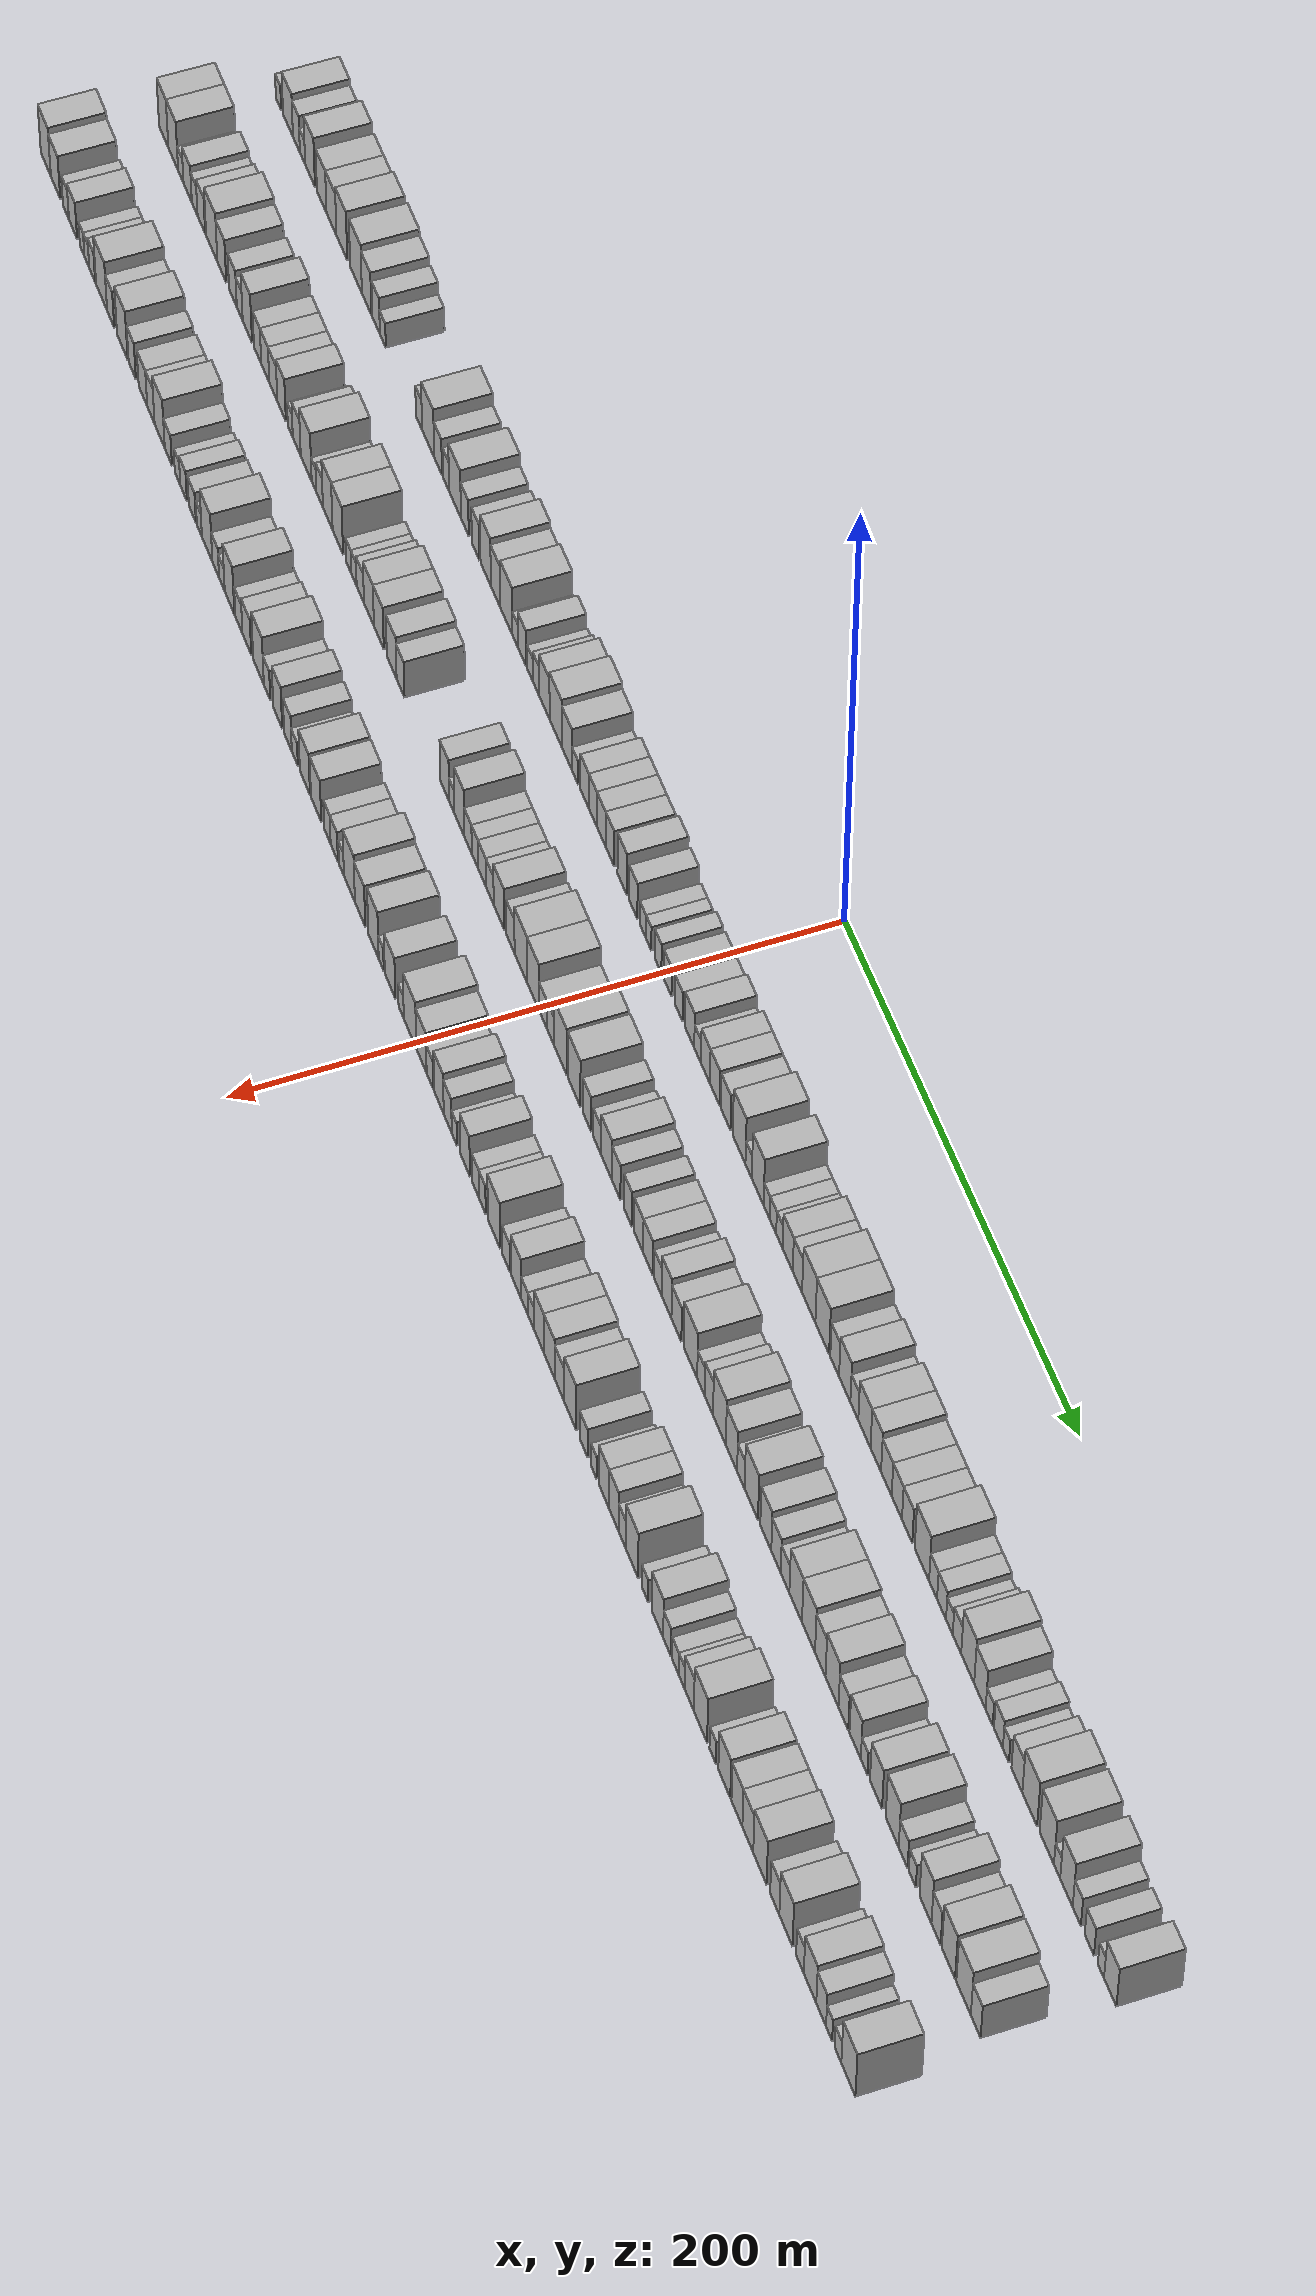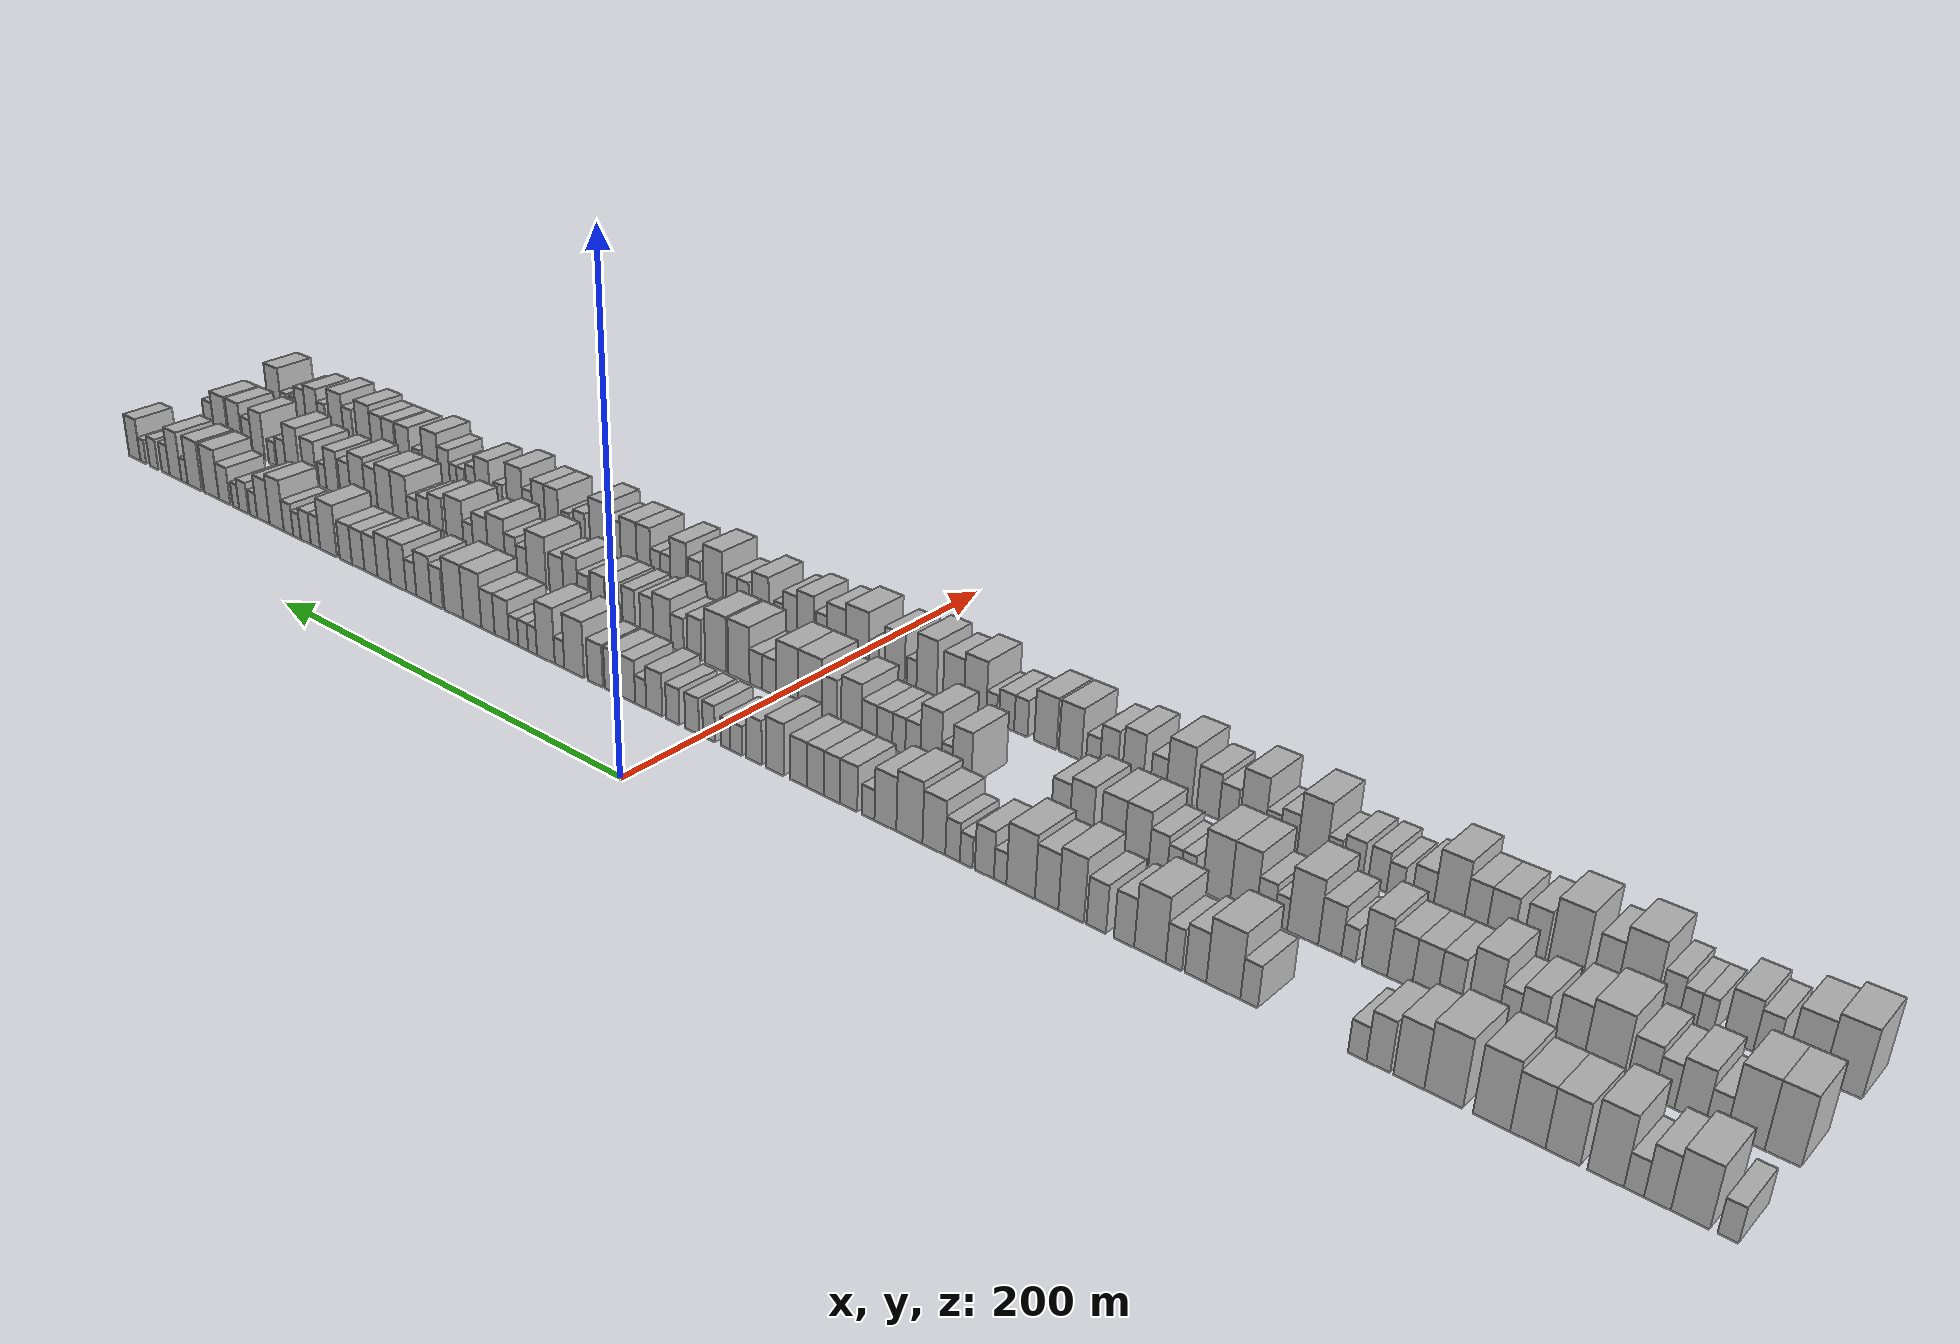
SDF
<sdf version="1.6">
 <world name="default">
  <scene>
   <sky><clouds><speed>12</speed></clouds></sky>
   <ambient>0.4 0.4 0.4 1</ambient>
   <background>0.7 0.7 0.7 1</background>
   <shadows>1</shadows>
  </scene>
  <gravity>0 0 -9.8066</gravity>
  <magnetic_field>6e-06 2.3e-05 -4.2e-05</magnetic_field>
  <physics default="0" name="default_physics" type="ode">
   <ode>
    <solver>
     <type>quick</type>
     <iters>10</iters>
     <sor>1.0</sor>
     <use_dynamic_moi_rescaling>0</use_dynamic_moi_rescaling>
    </solver>
    <constraints>
     <cfm>0</cfm>
     <erp>0.2</erp>
     <contact_max_correcting_vel>100</contact_max_correcting_vel>
     <contact_surface_layer>0.001</contact_surface_layer>
    </constraints>
   </ode>
   <max_step_size>0.004</max_step_size>
   <real_time_factor>1</real_time_factor>
   <real_time_update_rate>250</real_time_update_rate>
  </physics>
  <light name="sun" type="directional">
   <pose>0 0 10 0 0 0</pose>
   <diffuse>0.8 0.8 0.8 1</diffuse>
   <specular>0.2 0.2 0.2 1</specular>
   <attenuation>
    <range>1000</range>
    <constant>0.9</constant>
    <linear>0.01</linear>
    <quadratic>0.001</quadratic>
   </attenuation>
   <direction>-0.5 0.1 -0.9</direction>
  </light>
  <model name="building_1">
   <static>1</static>
   <pose>50.0000 -374.2624 0 0.000000 0.000000 0.000000</pose>
   <link name="link">
    <pose>0 0 6.00 0 0 0</pose>
    <collision name="collision"><geometry><box><size>20.0000 5.4753 12.0000</size></box></geometry></collision>
    <visual name="visual">
     <cast_shadows>0</cast_shadows>
     <geometry><box><size>20.0000 5.4753 12.0000</size></box></geometry>
     <material>
      <script>
       <uri>model://HANNAS_wall/materials/scripts</uri>
       <uri>model://HANNAS_wall/materials/textures</uri>
       <name>vrc/HANNAS_wall</name>
      </script>
     </material>
    </visual>
   </link>
  </model>
  <model name="building_2">
   <static>1</static>
   <pose>50.0000 -364.3549 0 0.000000 0.000000 0.000000</pose>
   <link name="link">
    <pose>0 0 10.50 0 0 0</pose>
    <collision name="collision"><geometry><box><size>20.0000 10.3397 21.0000</size></box></geometry></collision>
    <visual name="visual">
     <cast_shadows>0</cast_shadows>
     <geometry><box><size>20.0000 10.3397 21.0000</size></box></geometry>
     <material>
      <script>
       <uri>model://HANNAS_wall/materials/scripts</uri>
       <uri>model://HANNAS_wall/materials/textures</uri>
       <name>vrc/HANNAS_wall</name>
      </script>
     </material>
    </visual>
   </link>
  </model>
  <model name="building_3">
   <static>1</static>
   <pose>50.0000 -355.5785 0 0.000000 0.000000 0.000000</pose>
   <link name="link">
    <pose>0 0 9.00 0 0 0</pose>
    <collision name="collision"><geometry><box><size>20.0000 7.2129 18.0000</size></box></geometry></collision>
    <visual name="visual">
     <cast_shadows>0</cast_shadows>
     <geometry><box><size>20.0000 7.2129 18.0000</size></box></geometry>
     <material>
      <script>
       <uri>model://HANNAS_wall/materials/scripts</uri>
       <uri>model://HANNAS_wall/materials/textures</uri>
       <name>vrc/HANNAS_wall</name>
      </script>
     </material>
    </visual>
   </link>
  </model>
  <model name="building_4">
   <static>1</static>
   <pose>50.0000 -349.2453 0 0.000000 0.000000 0.000000</pose>
   <link name="link">
    <pose>0 0 6.00 0 0 0</pose>
    <collision name="collision"><geometry><box><size>20.0000 5.4536 12.0000</size></box></geometry></collision>
    <visual name="visual">
     <cast_shadows>0</cast_shadows>
     <geometry><box><size>20.0000 5.4536 12.0000</size></box></geometry>
     <material>
      <script>
       <uri>model://HANNAS_wall/materials/scripts</uri>
       <uri>model://HANNAS_wall/materials/textures</uri>
       <name>vrc/HANNAS_wall</name>
      </script>
     </material>
    </visual>
   </link>
  </model>
  <model name="building_5">
   <static>1</static>
   <pose>50.0000 -341.4378 0 0.000000 0.000000 0.000000</pose>
   <link name="link">
    <pose>0 0 12.00 0 0 0</pose>
    <collision name="collision"><geometry><box><size>20.0000 10.1614 24.0000</size></box></geometry></collision>
    <visual name="visual">
     <cast_shadows>0</cast_shadows>
     <geometry><box><size>20.0000 10.1614 24.0000</size></box></geometry>
     <material>
      <script>
       <uri>model://HANNAS_wall/materials/scripts</uri>
       <uri>model://HANNAS_wall/materials/textures</uri>
       <name>vrc/HANNAS_wall</name>
      </script>
     </material>
    </visual>
   </link>
  </model>
  <model name="building_6">
   <static>1</static>
   <pose>50.0000 -329.4169 0 0.000000 0.000000 0.000000</pose>
   <link name="link">
    <pose>0 0 10.50 0 0 0</pose>
    <collision name="collision"><geometry><box><size>20.0000 9.8803 21.0000</size></box></geometry></collision>
    <visual name="visual">
     <cast_shadows>0</cast_shadows>
     <geometry><box><size>20.0000 9.8803 21.0000</size></box></geometry>
     <material>
      <script>
       <uri>model://HANNAS_wall/materials/scripts</uri>
       <uri>model://HANNAS_wall/materials/textures</uri>
       <name>vrc/HANNAS_wall</name>
      </script>
     </material>
    </visual>
   </link>
  </model>
  <model name="building_7">
   <static>1</static>
   <pose>50.0000 -319.3622 0 0.000000 0.000000 0.000000</pose>
   <link name="link">
    <pose>0 0 10.50 0 0 0</pose>
    <collision name="collision"><geometry><box><size>20.0000 10.2292 21.0000</size></box></geometry></collision>
    <visual name="visual">
     <cast_shadows>0</cast_shadows>
     <geometry><box><size>20.0000 10.2292 21.0000</size></box></geometry>
     <material>
      <script>
       <uri>model://HANNAS_wall/materials/scripts</uri>
       <uri>model://HANNAS_wall/materials/textures</uri>
       <name>vrc/HANNAS_wall</name>
      </script>
     </material>
    </visual>
   </link>
  </model>
  <model name="building_8">
   <static>1</static>
   <pose>50.0000 -308.7134 0 0.000000 0.000000 0.000000</pose>
   <link name="link">
    <pose>0 0 12.00 0 0 0</pose>
    <collision name="collision"><geometry><box><size>20.0000 11.0682 24.0000</size></box></geometry></collision>
    <visual name="visual">
     <cast_shadows>0</cast_shadows>
     <geometry><box><size>20.0000 11.0682 24.0000</size></box></geometry>
     <material>
      <script>
       <uri>model://HANNAS_wall/materials/scripts</uri>
       <uri>model://HANNAS_wall/materials/textures</uri>
       <name>vrc/HANNAS_wall</name>
      </script>
     </material>
    </visual>
   </link>
  </model>
  <model name="building_9">
   <static>1</static>
   <pose>50.0000 -294.2568 0 0.000000 0.000000 0.000000</pose>
   <link name="link">
    <pose>0 0 12.00 0 0 0</pose>
    <collision name="collision"><geometry><box><size>20.0000 11.8451 24.0000</size></box></geometry></collision>
    <visual name="visual">
     <cast_shadows>0</cast_shadows>
     <geometry><box><size>20.0000 11.8451 24.0000</size></box></geometry>
     <material>
      <script>
       <uri>model://HANNAS_wall/materials/scripts</uri>
       <uri>model://HANNAS_wall/materials/textures</uri>
       <name>vrc/HANNAS_wall</name>
      </script>
     </material>
    </visual>
   </link>
  </model>
  <model name="building_10">
   <static>1</static>
   <pose>50.0000 -283.5182 0 0.000000 0.000000 0.000000</pose>
   <link name="link">
    <pose>0 0 10.50 0 0 0</pose>
    <collision name="collision"><geometry><box><size>20.0000 9.6320 21.0000</size></box></geometry></collision>
    <visual name="visual">
     <cast_shadows>0</cast_shadows>
     <geometry><box><size>20.0000 9.6320 21.0000</size></box></geometry>
     <material>
      <script>
       <uri>model://HANNAS_wall/materials/scripts</uri>
       <uri>model://HANNAS_wall/materials/textures</uri>
       <name>vrc/HANNAS_wall</name>
      </script>
     </material>
    </visual>
   </link>
  </model>
  <model name="building_11">
   <static>1</static>
   <pose>50.0000 -273.9121 0 0.000000 0.000000 0.000000</pose>
   <link name="link">
    <pose>0 0 9.00 0 0 0</pose>
    <collision name="collision"><geometry><box><size>20.0000 7.5804 18.0000</size></box></geometry></collision>
    <visual name="visual">
     <cast_shadows>0</cast_shadows>
     <geometry><box><size>20.0000 7.5804 18.0000</size></box></geometry>
     <material>
      <script>
       <uri>model://HANNAS_wall/materials/scripts</uri>
       <uri>model://HANNAS_wall/materials/textures</uri>
       <name>vrc/HANNAS_wall</name>
      </script>
     </material>
    </visual>
   </link>
  </model>
  <model name="building_12">
   <static>1</static>
   <pose>50.0000 -267.1441 0 0.000000 0.000000 0.000000</pose>
   <link name="link">
    <pose>0 0 6.00 0 0 0</pose>
    <collision name="collision"><geometry><box><size>20.0000 5.9556 12.0000</size></box></geometry></collision>
    <visual name="visual">
     <cast_shadows>0</cast_shadows>
     <geometry><box><size>20.0000 5.9556 12.0000</size></box></geometry>
     <material>
      <script>
       <uri>model://HANNAS_wall/materials/scripts</uri>
       <uri>model://HANNAS_wall/materials/textures</uri>
       <name>vrc/HANNAS_wall</name>
      </script>
     </material>
    </visual>
   </link>
  </model>
  <model name="building_13">
   <static>1</static>
   <pose>50.0000 -231.0191 0 0.000000 0.000000 0.000000</pose>
   <link name="link">
    <pose>0 0 7.50 0 0 0</pose>
    <collision name="collision"><geometry><box><size>20.0000 6.0981 15.0000</size></box></geometry></collision>
    <visual name="visual">
     <cast_shadows>0</cast_shadows>
     <geometry><box><size>20.0000 6.0981 15.0000</size></box></geometry>
     <material>
      <script>
       <uri>model://HANNAS_wall/materials/scripts</uri>
       <uri>model://HANNAS_wall/materials/textures</uri>
       <name>vrc/HANNAS_wall</name>
      </script>
     </material>
    </visual>
   </link>
  </model>
  <model name="building_14">
   <static>1</static>
   <pose>50.0000 -221.9719 0 0.000000 0.000000 0.000000</pose>
   <link name="link">
    <pose>0 0 12.00 0 0 0</pose>
    <collision name="collision"><geometry><box><size>20.0000 11.9962 24.0000</size></box></geometry></collision>
    <visual name="visual">
     <cast_shadows>0</cast_shadows>
     <geometry><box><size>20.0000 11.9962 24.0000</size></box></geometry>
     <material>
      <script>
       <uri>model://HANNAS_wall/materials/scripts</uri>
       <uri>model://HANNAS_wall/materials/textures</uri>
       <name>vrc/HANNAS_wall</name>
      </script>
     </material>
    </visual>
   </link>
  </model>
  <model name="building_15">
   <static>1</static>
   <pose>50.0000 -212.1358 0 0.000000 0.000000 0.000000</pose>
   <link name="link">
    <pose>0 0 9.00 0 0 0</pose>
    <collision name="collision"><geometry><box><size>20.0000 7.6759 18.0000</size></box></geometry></collision>
    <visual name="visual">
     <cast_shadows>0</cast_shadows>
     <geometry><box><size>20.0000 7.6759 18.0000</size></box></geometry>
     <material>
      <script>
       <uri>model://HANNAS_wall/materials/scripts</uri>
       <uri>model://HANNAS_wall/materials/textures</uri>
       <name>vrc/HANNAS_wall</name>
      </script>
     </material>
    </visual>
   </link>
  </model>
  <model name="building_16">
   <static>1</static>
   <pose>50.0000 -204.2858 0 0.000000 0.000000 0.000000</pose>
   <link name="link">
    <pose>0 0 7.50 0 0 0</pose>
    <collision name="collision"><geometry><box><size>20.0000 6.0241 15.0000</size></box></geometry></collision>
    <visual name="visual">
     <cast_shadows>0</cast_shadows>
     <geometry><box><size>20.0000 6.0241 15.0000</size></box></geometry>
     <material>
      <script>
       <uri>model://HANNAS_wall/materials/scripts</uri>
       <uri>model://HANNAS_wall/materials/textures</uri>
       <name>vrc/HANNAS_wall</name>
      </script>
     </material>
    </visual>
   </link>
  </model>
  <model name="building_17">
   <static>1</static>
   <pose>50.0000 -195.4628 0 0.000000 0.000000 0.000000</pose>
   <link name="link">
    <pose>0 0 12.00 0 0 0</pose>
    <collision name="collision"><geometry><box><size>20.0000 11.6219 24.0000</size></box></geometry></collision>
    <visual name="visual">
     <cast_shadows>0</cast_shadows>
     <geometry><box><size>20.0000 11.6219 24.0000</size></box></geometry>
     <material>
      <script>
       <uri>model://HANNAS_wall/materials/scripts</uri>
       <uri>model://HANNAS_wall/materials/textures</uri>
       <name>vrc/HANNAS_wall</name>
      </script>
     </material>
    </visual>
   </link>
  </model>
  <model name="building_18">
   <static>1</static>
   <pose>50.0000 -185.8370 0 0.000000 0.000000 0.000000</pose>
   <link name="link">
    <pose>0 0 9.00 0 0 0</pose>
    <collision name="collision"><geometry><box><size>20.0000 7.6296 18.0000</size></box></geometry></collision>
    <visual name="visual">
     <cast_shadows>0</cast_shadows>
     <geometry><box><size>20.0000 7.6296 18.0000</size></box></geometry>
     <material>
      <script>
       <uri>model://HANNAS_wall/materials/scripts</uri>
       <uri>model://HANNAS_wall/materials/textures</uri>
       <name>vrc/HANNAS_wall</name>
      </script>
     </material>
    </visual>
   </link>
  </model>
  <model name="building_19">
   <static>1</static>
   <pose>50.0000 -175.2739 0 0.000000 0.000000 0.000000</pose>
   <link name="link">
    <pose>0 0 9.00 0 0 0</pose>
    <collision name="collision"><geometry><box><size>20.0000 7.4967 18.0000</size></box></geometry></collision>
    <visual name="visual">
     <cast_shadows>0</cast_shadows>
     <geometry><box><size>20.0000 7.4967 18.0000</size></box></geometry>
     <material>
      <script>
       <uri>model://HANNAS_wall/materials/scripts</uri>
       <uri>model://HANNAS_wall/materials/textures</uri>
       <name>vrc/HANNAS_wall</name>
      </script>
     </material>
    </visual>
   </link>
  </model>
  <model name="building_20">
   <static>1</static>
   <pose>50.0000 -165.5309 0 0.000000 0.000000 0.000000</pose>
   <link name="link">
    <pose>0 0 12.00 0 0 0</pose>
    <collision name="collision"><geometry><box><size>20.0000 9.9893 24.0000</size></box></geometry></collision>
    <visual name="visual">
     <cast_shadows>0</cast_shadows>
     <geometry><box><size>20.0000 9.9893 24.0000</size></box></geometry>
     <material>
      <script>
       <uri>model://HANNAS_wall/materials/scripts</uri>
       <uri>model://HANNAS_wall/materials/textures</uri>
       <name>vrc/HANNAS_wall</name>
      </script>
     </material>
    </visual>
   </link>
  </model>
  <model name="building_21">
   <static>1</static>
   <pose>50.0000 -155.8744 0 0.000000 0.000000 0.000000</pose>
   <link name="link">
    <pose>0 0 10.50 0 0 0</pose>
    <collision name="collision"><geometry><box><size>20.0000 9.3238 21.0000</size></box></geometry></collision>
    <visual name="visual">
     <cast_shadows>0</cast_shadows>
     <geometry><box><size>20.0000 9.3238 21.0000</size></box></geometry>
     <material>
      <script>
       <uri>model://HANNAS_wall/materials/scripts</uri>
       <uri>model://HANNAS_wall/materials/textures</uri>
       <name>vrc/HANNAS_wall</name>
      </script>
     </material>
    </visual>
   </link>
  </model>
  <model name="building_22">
   <static>1</static>
   <pose>50.0000 -145.4319 0 0.000000 0.000000 0.000000</pose>
   <link name="link">
    <pose>0 0 12.00 0 0 0</pose>
    <collision name="collision"><geometry><box><size>20.0000 11.5612 24.0000</size></box></geometry></collision>
    <visual name="visual">
     <cast_shadows>0</cast_shadows>
     <geometry><box><size>20.0000 11.5612 24.0000</size></box></geometry>
     <material>
      <script>
       <uri>model://HANNAS_wall/materials/scripts</uri>
       <uri>model://HANNAS_wall/materials/textures</uri>
       <name>vrc/HANNAS_wall</name>
      </script>
     </material>
    </visual>
   </link>
  </model>
  <model name="building_23">
   <static>1</static>
   <pose>50.0000 -137.0996 0 0.000000 0.000000 0.000000</pose>
   <link name="link">
    <pose>0 0 6.00 0 0 0</pose>
    <collision name="collision"><geometry><box><size>20.0000 5.1034 12.0000</size></box></geometry></collision>
    <visual name="visual">
     <cast_shadows>0</cast_shadows>
     <geometry><box><size>20.0000 5.1034 12.0000</size></box></geometry>
     <material>
      <script>
       <uri>model://HANNAS_wall/materials/scripts</uri>
       <uri>model://HANNAS_wall/materials/textures</uri>
       <name>vrc/HANNAS_wall</name>
      </script>
     </material>
    </visual>
   </link>
  </model>
  <model name="building_24">
   <static>1</static>
   <pose>50.0000 -130.5739 0 0.000000 0.000000 0.000000</pose>
   <link name="link">
    <pose>0 0 9.00 0 0 0</pose>
    <collision name="collision"><geometry><box><size>20.0000 7.9480 18.0000</size></box></geometry></collision>
    <visual name="visual">
     <cast_shadows>0</cast_shadows>
     <geometry><box><size>20.0000 7.9480 18.0000</size></box></geometry>
     <material>
      <script>
       <uri>model://HANNAS_wall/materials/scripts</uri>
       <uri>model://HANNAS_wall/materials/textures</uri>
       <name>vrc/HANNAS_wall</name>
      </script>
     </material>
    </visual>
   </link>
  </model>
  <model name="building_25">
   <static>1</static>
   <pose>50.0000 -122.9616 0 0.000000 0.000000 0.000000</pose>
   <link name="link">
    <pose>0 0 6.00 0 0 0</pose>
    <collision name="collision"><geometry><box><size>20.0000 5.2764 12.0000</size></box></geometry></collision>
    <visual name="visual">
     <cast_shadows>0</cast_shadows>
     <geometry><box><size>20.0000 5.2764 12.0000</size></box></geometry>
     <material>
      <script>
       <uri>model://HANNAS_wall/materials/scripts</uri>
       <uri>model://HANNAS_wall/materials/textures</uri>
       <name>vrc/HANNAS_wall</name>
      </script>
     </material>
    </visual>
   </link>
  </model>
  <model name="building_26">
   <static>1</static>
   <pose>50.0000 -117.2338 0 0.000000 0.000000 0.000000</pose>
   <link name="link">
    <pose>0 0 7.50 0 0 0</pose>
    <collision name="collision"><geometry><box><size>20.0000 6.1794 15.0000</size></box></geometry></collision>
    <visual name="visual">
     <cast_shadows>0</cast_shadows>
     <geometry><box><size>20.0000 6.1794 15.0000</size></box></geometry>
     <material>
      <script>
       <uri>model://HANNAS_wall/materials/scripts</uri>
       <uri>model://HANNAS_wall/materials/textures</uri>
       <name>vrc/HANNAS_wall</name>
      </script>
     </material>
    </visual>
   </link>
  </model>
  <model name="building_27">
   <static>1</static>
   <pose>50.0000 -109.2089 0 0.000000 0.000000 0.000000</pose>
   <link name="link">
    <pose>0 0 10.50 0 0 0</pose>
    <collision name="collision"><geometry><box><size>20.0000 9.8703 21.0000</size></box></geometry></collision>
    <visual name="visual">
     <cast_shadows>0</cast_shadows>
     <geometry><box><size>20.0000 9.8703 21.0000</size></box></geometry>
     <material>
      <script>
       <uri>model://HANNAS_wall/materials/scripts</uri>
       <uri>model://HANNAS_wall/materials/textures</uri>
       <name>vrc/HANNAS_wall</name>
      </script>
     </material>
    </visual>
   </link>
  </model>
  <model name="building_28">
   <static>1</static>
   <pose>50.0000 -98.5389 0 0.000000 0.000000 0.000000</pose>
   <link name="link">
    <pose>0 0 12.00 0 0 0</pose>
    <collision name="collision"><geometry><box><size>20.0000 11.4696 24.0000</size></box></geometry></collision>
    <visual name="visual">
     <cast_shadows>0</cast_shadows>
     <geometry><box><size>20.0000 11.4696 24.0000</size></box></geometry>
     <material>
      <script>
       <uri>model://HANNAS_wall/materials/scripts</uri>
       <uri>model://HANNAS_wall/materials/textures</uri>
       <name>vrc/HANNAS_wall</name>
      </script>
     </material>
    </visual>
   </link>
  </model>
  <model name="building_29">
   <static>1</static>
   <pose>50.0000 -87.9355 0 0.000000 0.000000 0.000000</pose>
   <link name="link">
    <pose>0 0 10.50 0 0 0</pose>
    <collision name="collision"><geometry><box><size>20.0000 9.7372 21.0000</size></box></geometry></collision>
    <visual name="visual">
     <cast_shadows>0</cast_shadows>
     <geometry><box><size>20.0000 9.7372 21.0000</size></box></geometry>
     <material>
      <script>
       <uri>model://HANNAS_wall/materials/scripts</uri>
       <uri>model://HANNAS_wall/materials/textures</uri>
       <name>vrc/HANNAS_wall</name>
      </script>
     </material>
    </visual>
   </link>
  </model>
  <model name="building_30">
   <static>1</static>
   <pose>50.0000 -80.1700 0 0.000000 0.000000 0.000000</pose>
   <link name="link">
    <pose>0 0 6.00 0 0 0</pose>
    <collision name="collision"><geometry><box><size>20.0000 5.7939 12.0000</size></box></geometry></collision>
    <visual name="visual">
     <cast_shadows>0</cast_shadows>
     <geometry><box><size>20.0000 5.7939 12.0000</size></box></geometry>
     <material>
      <script>
       <uri>model://HANNAS_wall/materials/scripts</uri>
       <uri>model://HANNAS_wall/materials/textures</uri>
       <name>vrc/HANNAS_wall</name>
      </script>
     </material>
    </visual>
   </link>
  </model>
  <model name="building_31">
   <static>1</static>
   <pose>50.0000 -71.2959 0 0.000000 0.000000 0.000000</pose>
   <link name="link">
    <pose>0 0 9.00 0 0 0</pose>
    <collision name="collision"><geometry><box><size>20.0000 7.9543 18.0000</size></box></geometry></collision>
    <visual name="visual">
     <cast_shadows>0</cast_shadows>
     <geometry><box><size>20.0000 7.9543 18.0000</size></box></geometry>
     <material>
      <script>
       <uri>model://HANNAS_wall/materials/scripts</uri>
       <uri>model://HANNAS_wall/materials/textures</uri>
       <name>vrc/HANNAS_wall</name>
      </script>
     </material>
    </visual>
   </link>
  </model>
  <model name="building_32">
   <static>1</static>
   <pose>50.0000 -63.6211 0 0.000000 0.000000 0.000000</pose>
   <link name="link">
    <pose>0 0 9.00 0 0 0</pose>
    <collision name="collision"><geometry><box><size>20.0000 7.3951 18.0000</size></box></geometry></collision>
    <visual name="visual">
     <cast_shadows>0</cast_shadows>
     <geometry><box><size>20.0000 7.3951 18.0000</size></box></geometry>
     <material>
      <script>
       <uri>model://HANNAS_wall/materials/scripts</uri>
       <uri>model://HANNAS_wall/materials/textures</uri>
       <name>vrc/HANNAS_wall</name>
      </script>
     </material>
    </visual>
   </link>
  </model>
  <model name="building_33">
   <static>1</static>
   <pose>50.0000 -55.8472 0 0.000000 0.000000 0.000000</pose>
   <link name="link">
    <pose>0 0 9.00 0 0 0</pose>
    <collision name="collision"><geometry><box><size>20.0000 8.1526 18.0000</size></box></geometry></collision>
    <visual name="visual">
     <cast_shadows>0</cast_shadows>
     <geometry><box><size>20.0000 8.1526 18.0000</size></box></geometry>
     <material>
      <script>
       <uri>model://HANNAS_wall/materials/scripts</uri>
       <uri>model://HANNAS_wall/materials/textures</uri>
       <name>vrc/HANNAS_wall</name>
      </script>
     </material>
    </visual>
   </link>
  </model>
  <model name="building_34">
   <static>1</static>
   <pose>50.0000 -47.7403 0 0.000000 0.000000 0.000000</pose>
   <link name="link">
    <pose>0 0 9.00 0 0 0</pose>
    <collision name="collision"><geometry><box><size>20.0000 8.0612 18.0000</size></box></geometry></collision>
    <visual name="visual">
     <cast_shadows>0</cast_shadows>
     <geometry><box><size>20.0000 8.0612 18.0000</size></box></geometry>
     <material>
      <script>
       <uri>model://HANNAS_wall/materials/scripts</uri>
       <uri>model://HANNAS_wall/materials/textures</uri>
       <name>vrc/HANNAS_wall</name>
      </script>
     </material>
    </visual>
   </link>
  </model>
  <model name="building_35">
   <static>1</static>
   <pose>50.0000 -36.3752 0 0.000000 0.000000 0.000000</pose>
   <link name="link">
    <pose>0 0 10.50 0 0 0</pose>
    <collision name="collision"><geometry><box><size>20.0000 8.6689 21.0000</size></box></geometry></collision>
    <visual name="visual">
     <cast_shadows>0</cast_shadows>
     <geometry><box><size>20.0000 8.6689 21.0000</size></box></geometry>
     <material>
      <script>
       <uri>model://HANNAS_wall/materials/scripts</uri>
       <uri>model://HANNAS_wall/materials/textures</uri>
       <name>vrc/HANNAS_wall</name>
      </script>
     </material>
    </visual>
   </link>
  </model>
  <model name="building_36">
   <static>1</static>
   <pose>50.0000 -26.2224 0 0.000000 0.000000 0.000000</pose>
   <link name="link">
    <pose>0 0 9.00 0 0 0</pose>
    <collision name="collision"><geometry><box><size>20.0000 7.6368 18.0000</size></box></geometry></collision>
    <visual name="visual">
     <cast_shadows>0</cast_shadows>
     <geometry><box><size>20.0000 7.6368 18.0000</size></box></geometry>
     <material>
      <script>
       <uri>model://HANNAS_wall/materials/scripts</uri>
       <uri>model://HANNAS_wall/materials/textures</uri>
       <name>vrc/HANNAS_wall</name>
      </script>
     </material>
    </visual>
   </link>
  </model>
  <model name="building_37">
   <static>1</static>
   <pose>50.0000 -17.4425 0 0.000000 0.000000 0.000000</pose>
   <link name="link">
    <pose>0 0 6.00 0 0 0</pose>
    <collision name="collision"><geometry><box><size>20.0000 5.9229 12.0000</size></box></geometry></collision>
    <visual name="visual">
     <cast_shadows>0</cast_shadows>
     <geometry><box><size>20.0000 5.9229 12.0000</size></box></geometry>
     <material>
      <script>
       <uri>model://HANNAS_wall/materials/scripts</uri>
       <uri>model://HANNAS_wall/materials/textures</uri>
       <name>vrc/HANNAS_wall</name>
      </script>
     </material>
    </visual>
   </link>
  </model>
  <model name="building_38">
   <static>1</static>
   <pose>50.0000 -12.0507 0 0.000000 0.000000 0.000000</pose>
   <link name="link">
    <pose>0 0 6.00 0 0 0</pose>
    <collision name="collision"><geometry><box><size>20.0000 4.8607 12.0000</size></box></geometry></collision>
    <visual name="visual">
     <cast_shadows>0</cast_shadows>
     <geometry><box><size>20.0000 4.8607 12.0000</size></box></geometry>
     <material>
      <script>
       <uri>model://HANNAS_wall/materials/scripts</uri>
       <uri>model://HANNAS_wall/materials/textures</uri>
       <name>vrc/HANNAS_wall</name>
      </script>
     </material>
    </visual>
   </link>
  </model>
  <model name="building_39">
   <static>1</static>
   <pose>50.0000 -3.5310 0 0.000000 0.000000 0.000000</pose>
   <link name="link">
    <pose>0 0 7.50 0 0 0</pose>
    <collision name="collision"><geometry><box><size>20.0000 6.1787 15.0000</size></box></geometry></collision>
    <visual name="visual">
     <cast_shadows>0</cast_shadows>
     <geometry><box><size>20.0000 6.1787 15.0000</size></box></geometry>
     <material>
      <script>
       <uri>model://HANNAS_wall/materials/scripts</uri>
       <uri>model://HANNAS_wall/materials/textures</uri>
       <name>vrc/HANNAS_wall</name>
      </script>
     </material>
    </visual>
   </link>
  </model>
  <model name="building_40">
   <static>1</static>
   <pose>50.0000 5.1485 0 0.000000 0.000000 0.000000</pose>
   <link name="link">
    <pose>0 0 7.50 0 0 0</pose>
    <collision name="collision"><geometry><box><size>20.0000 7.1804 15.0000</size></box></geometry></collision>
    <visual name="visual">
     <cast_shadows>0</cast_shadows>
     <geometry><box><size>20.0000 7.1804 15.0000</size></box></geometry>
     <material>
      <script>
       <uri>model://HANNAS_wall/materials/scripts</uri>
       <uri>model://HANNAS_wall/materials/textures</uri>
       <name>vrc/HANNAS_wall</name>
      </script>
     </material>
    </visual>
   </link>
  </model>
  <model name="building_41">
   <static>1</static>
   <pose>50.0000 15.2421 0 0.000000 0.000000 0.000000</pose>
   <link name="link">
    <pose>0 0 7.50 0 0 0</pose>
    <collision name="collision"><geometry><box><size>20.0000 7.0069 15.0000</size></box></geometry></collision>
    <visual name="visual">
     <cast_shadows>0</cast_shadows>
     <geometry><box><size>20.0000 7.0069 15.0000</size></box></geometry>
     <material>
      <script>
       <uri>model://HANNAS_wall/materials/scripts</uri>
       <uri>model://HANNAS_wall/materials/textures</uri>
       <name>vrc/HANNAS_wall</name>
      </script>
     </material>
    </visual>
   </link>
  </model>
  <model name="building_42">
   <static>1</static>
   <pose>50.0000 25.0485 0 0.000000 0.000000 0.000000</pose>
   <link name="link">
    <pose>0 0 9.00 0 0 0</pose>
    <collision name="collision"><geometry><box><size>20.0000 8.6059 18.0000</size></box></geometry></collision>
    <visual name="visual">
     <cast_shadows>0</cast_shadows>
     <geometry><box><size>20.0000 8.6059 18.0000</size></box></geometry>
     <material>
      <script>
       <uri>model://HANNAS_wall/materials/scripts</uri>
       <uri>model://HANNAS_wall/materials/textures</uri>
       <name>vrc/HANNAS_wall</name>
      </script>
     </material>
    </visual>
   </link>
  </model>
  <model name="building_43">
   <static>1</static>
   <pose>50.0000 32.3402 0 0.000000 0.000000 0.000000</pose>
   <link name="link">
    <pose>0 0 6.00 0 0 0</pose>
    <collision name="collision"><geometry><box><size>20.0000 5.9775 12.0000</size></box></geometry></collision>
    <visual name="visual">
     <cast_shadows>0</cast_shadows>
     <geometry><box><size>20.0000 5.9775 12.0000</size></box></geometry>
     <material>
      <script>
       <uri>model://HANNAS_wall/materials/scripts</uri>
       <uri>model://HANNAS_wall/materials/textures</uri>
       <name>vrc/HANNAS_wall</name>
      </script>
     </material>
    </visual>
   </link>
  </model>
  <model name="building_44">
   <static>1</static>
   <pose>50.0000 39.3479 0 0.000000 0.000000 0.000000</pose>
   <link name="link">
    <pose>0 0 9.00 0 0 0</pose>
    <collision name="collision"><geometry><box><size>20.0000 8.0379 18.0000</size></box></geometry></collision>
    <visual name="visual">
     <cast_shadows>0</cast_shadows>
     <geometry><box><size>20.0000 8.0379 18.0000</size></box></geometry>
     <material>
      <script>
       <uri>model://HANNAS_wall/materials/scripts</uri>
       <uri>model://HANNAS_wall/materials/textures</uri>
       <name>vrc/HANNAS_wall</name>
      </script>
     </material>
    </visual>
   </link>
  </model>
  <model name="building_45">
   <static>1</static>
   <pose>50.0000 47.7327 0 0.000000 0.000000 0.000000</pose>
   <link name="link">
    <pose>0 0 9.00 0 0 0</pose>
    <collision name="collision"><geometry><box><size>20.0000 8.7317 18.0000</size></box></geometry></collision>
    <visual name="visual">
     <cast_shadows>0</cast_shadows>
     <geometry><box><size>20.0000 8.7317 18.0000</size></box></geometry>
     <material>
      <script>
       <uri>model://HANNAS_wall/materials/scripts</uri>
       <uri>model://HANNAS_wall/materials/textures</uri>
       <name>vrc/HANNAS_wall</name>
      </script>
     </material>
    </visual>
   </link>
  </model>
  <model name="building_46">
   <static>1</static>
   <pose>50.0000 57.4240 0 0.000000 0.000000 0.000000</pose>
   <link name="link">
    <pose>0 0 9.00 0 0 0</pose>
    <collision name="collision"><geometry><box><size>20.0000 8.6509 18.0000</size></box></geometry></collision>
    <visual name="visual">
     <cast_shadows>0</cast_shadows>
     <geometry><box><size>20.0000 8.6509 18.0000</size></box></geometry>
     <material>
      <script>
       <uri>model://HANNAS_wall/materials/scripts</uri>
       <uri>model://HANNAS_wall/materials/textures</uri>
       <name>vrc/HANNAS_wall</name>
      </script>
     </material>
    </visual>
   </link>
  </model>
  <model name="building_47">
   <static>1</static>
   <pose>50.0000 69.3902 0 0.000000 0.000000 0.000000</pose>
   <link name="link">
    <pose>0 0 12.00 0 0 0</pose>
    <collision name="collision"><geometry><box><size>20.0000 11.2815 24.0000</size></box></geometry></collision>
    <visual name="visual">
     <cast_shadows>0</cast_shadows>
     <geometry><box><size>20.0000 11.2815 24.0000</size></box></geometry>
     <material>
      <script>
       <uri>model://HANNAS_wall/materials/scripts</uri>
       <uri>model://HANNAS_wall/materials/textures</uri>
       <name>vrc/HANNAS_wall</name>
      </script>
     </material>
    </visual>
   </link>
  </model>
  <model name="building_48">
   <static>1</static>
   <pose>50.0000 77.8082 0 0.000000 0.000000 0.000000</pose>
   <link name="link">
    <pose>0 0 6.00 0 0 0</pose>
    <collision name="collision"><geometry><box><size>20.0000 5.5546 12.0000</size></box></geometry></collision>
    <visual name="visual">
     <cast_shadows>0</cast_shadows>
     <geometry><box><size>20.0000 5.5546 12.0000</size></box></geometry>
     <material>
      <script>
       <uri>model://HANNAS_wall/materials/scripts</uri>
       <uri>model://HANNAS_wall/materials/textures</uri>
       <name>vrc/HANNAS_wall</name>
      </script>
     </material>
    </visual>
   </link>
  </model>
  <model name="building_49">
   <static>1</static>
   <pose>50.0000 85.8110 0 0.000000 0.000000 0.000000</pose>
   <link name="link">
    <pose>0 0 12.00 0 0 0</pose>
    <collision name="collision"><geometry><box><size>20.0000 10.4510 24.0000</size></box></geometry></collision>
    <visual name="visual">
     <cast_shadows>0</cast_shadows>
     <geometry><box><size>20.0000 10.4510 24.0000</size></box></geometry>
     <material>
      <script>
       <uri>model://HANNAS_wall/materials/scripts</uri>
       <uri>model://HANNAS_wall/materials/textures</uri>
       <name>vrc/HANNAS_wall</name>
      </script>
     </material>
    </visual>
   </link>
  </model>
  <model name="building_50">
   <static>1</static>
   <pose>50.0000 93.6552 0 0.000000 0.000000 0.000000</pose>
   <link name="link">
    <pose>0 0 6.00 0 0 0</pose>
    <collision name="collision"><geometry><box><size>20.0000 5.2373 12.0000</size></box></geometry></collision>
    <visual name="visual">
     <cast_shadows>0</cast_shadows>
     <geometry><box><size>20.0000 5.2373 12.0000</size></box></geometry>
     <material>
      <script>
       <uri>model://HANNAS_wall/materials/scripts</uri>
       <uri>model://HANNAS_wall/materials/textures</uri>
       <name>vrc/HANNAS_wall</name>
      </script>
     </material>
    </visual>
   </link>
  </model>
  <model name="building_51">
   <static>1</static>
   <pose>50.0000 99.1758 0 0.000000 0.000000 0.000000</pose>
   <link name="link">
    <pose>0 0 6.00 0 0 0</pose>
    <collision name="collision"><geometry><box><size>20.0000 5.8039 12.0000</size></box></geometry></collision>
    <visual name="visual">
     <cast_shadows>0</cast_shadows>
     <geometry><box><size>20.0000 5.8039 12.0000</size></box></geometry>
     <material>
      <script>
       <uri>model://HANNAS_wall/materials/scripts</uri>
       <uri>model://HANNAS_wall/materials/textures</uri>
       <name>vrc/HANNAS_wall</name>
      </script>
     </material>
    </visual>
   </link>
  </model>
  <model name="building_52">
   <static>1</static>
   <pose>50.0000 104.8412 0 0.000000 0.000000 0.000000</pose>
   <link name="link">
    <pose>0 0 6.00 0 0 0</pose>
    <collision name="collision"><geometry><box><size>20.0000 5.5271 12.0000</size></box></geometry></collision>
    <visual name="visual">
     <cast_shadows>0</cast_shadows>
     <geometry><box><size>20.0000 5.5271 12.0000</size></box></geometry>
     <material>
      <script>
       <uri>model://HANNAS_wall/materials/scripts</uri>
       <uri>model://HANNAS_wall/materials/textures</uri>
       <name>vrc/HANNAS_wall</name>
      </script>
     </material>
    </visual>
   </link>
  </model>
  <model name="building_53">
   <static>1</static>
   <pose>50.0000 112.0588 0 0.000000 0.000000 0.000000</pose>
   <link name="link">
    <pose>0 0 9.00 0 0 0</pose>
    <collision name="collision"><geometry><box><size>20.0000 8.9081 18.0000</size></box></geometry></collision>
    <visual name="visual">
     <cast_shadows>0</cast_shadows>
     <geometry><box><size>20.0000 8.9081 18.0000</size></box></geometry>
     <material>
      <script>
       <uri>model://HANNAS_wall/materials/scripts</uri>
       <uri>model://HANNAS_wall/materials/textures</uri>
       <name>vrc/HANNAS_wall</name>
      </script>
     </material>
    </visual>
   </link>
  </model>
  <model name="building_54">
   <static>1</static>
   <pose>50.0000 120.5730 0 0.000000 0.000000 0.000000</pose>
   <link name="link">
    <pose>0 0 9.00 0 0 0</pose>
    <collision name="collision"><geometry><box><size>20.0000 8.1203 18.0000</size></box></geometry></collision>
    <visual name="visual">
     <cast_shadows>0</cast_shadows>
     <geometry><box><size>20.0000 8.1203 18.0000</size></box></geometry>
     <material>
      <script>
       <uri>model://HANNAS_wall/materials/scripts</uri>
       <uri>model://HANNAS_wall/materials/textures</uri>
       <name>vrc/HANNAS_wall</name>
      </script>
     </material>
    </visual>
   </link>
  </model>
  <model name="building_55">
   <static>1</static>
   <pose>50.0000 130.3924 0 0.000000 0.000000 0.000000</pose>
   <link name="link">
    <pose>0 0 12.00 0 0 0</pose>
    <collision name="collision"><geometry><box><size>20.0000 11.5184 24.0000</size></box></geometry></collision>
    <visual name="visual">
     <cast_shadows>0</cast_shadows>
     <geometry><box><size>20.0000 11.5184 24.0000</size></box></geometry>
     <material>
      <script>
       <uri>model://HANNAS_wall/materials/scripts</uri>
       <uri>model://HANNAS_wall/materials/textures</uri>
       <name>vrc/HANNAS_wall</name>
      </script>
     </material>
    </visual>
   </link>
  </model>
  <model name="building_56">
   <static>1</static>
   <pose>50.0000 142.0532 0 0.000000 0.000000 0.000000</pose>
   <link name="link">
    <pose>0 0 12.00 0 0 0</pose>
    <collision name="collision"><geometry><box><size>20.0000 11.8031 24.0000</size></box></geometry></collision>
    <visual name="visual">
     <cast_shadows>0</cast_shadows>
     <geometry><box><size>20.0000 11.8031 24.0000</size></box></geometry>
     <material>
      <script>
       <uri>model://HANNAS_wall/materials/scripts</uri>
       <uri>model://HANNAS_wall/materials/textures</uri>
       <name>vrc/HANNAS_wall</name>
      </script>
     </material>
    </visual>
   </link>
  </model>
  <model name="building_57">
   <static>1</static>
   <pose>50.0000 152.7229 0 0.000000 0.000000 0.000000</pose>
   <link name="link">
    <pose>0 0 9.00 0 0 0</pose>
    <collision name="collision"><geometry><box><size>20.0000 7.5364 18.0000</size></box></geometry></collision>
    <visual name="visual">
     <cast_shadows>0</cast_shadows>
     <geometry><box><size>20.0000 7.5364 18.0000</size></box></geometry>
     <material>
      <script>
       <uri>model://HANNAS_wall/materials/scripts</uri>
       <uri>model://HANNAS_wall/materials/textures</uri>
       <name>vrc/HANNAS_wall</name>
      </script>
     </material>
    </visual>
   </link>
  </model>
  <model name="building_58">
   <static>1</static>
   <pose>50.0000 161.3210 0 0.000000 0.000000 0.000000</pose>
   <link name="link">
    <pose>0 0 10.50 0 0 0</pose>
    <collision name="collision"><geometry><box><size>20.0000 9.6599 21.0000</size></box></geometry></collision>
    <visual name="visual">
     <cast_shadows>0</cast_shadows>
     <geometry><box><size>20.0000 9.6599 21.0000</size></box></geometry>
     <material>
      <script>
       <uri>model://HANNAS_wall/materials/scripts</uri>
       <uri>model://HANNAS_wall/materials/textures</uri>
       <name>vrc/HANNAS_wall</name>
      </script>
     </material>
    </visual>
   </link>
  </model>
  <model name="building_59">
   <static>1</static>
   <pose>50.0000 169.5374 0 0.000000 0.000000 0.000000</pose>
   <link name="link">
    <pose>0 0 7.50 0 0 0</pose>
    <collision name="collision"><geometry><box><size>20.0000 6.7729 15.0000</size></box></geometry></collision>
    <visual name="visual">
     <cast_shadows>0</cast_shadows>
     <geometry><box><size>20.0000 6.7729 15.0000</size></box></geometry>
     <material>
      <script>
       <uri>model://HANNAS_wall/materials/scripts</uri>
       <uri>model://HANNAS_wall/materials/textures</uri>
       <name>vrc/HANNAS_wall</name>
      </script>
     </material>
    </visual>
   </link>
  </model>
  <model name="building_60">
   <static>1</static>
   <pose>50.0000 178.0933 0 0.000000 0.000000 0.000000</pose>
   <link name="link">
    <pose>0 0 10.50 0 0 0</pose>
    <collision name="collision"><geometry><box><size>20.0000 10.3389 21.0000</size></box></geometry></collision>
    <visual name="visual">
     <cast_shadows>0</cast_shadows>
     <geometry><box><size>20.0000 10.3389 21.0000</size></box></geometry>
     <material>
      <script>
       <uri>model://HANNAS_wall/materials/scripts</uri>
       <uri>model://HANNAS_wall/materials/textures</uri>
       <name>vrc/HANNAS_wall</name>
      </script>
     </material>
    </visual>
   </link>
  </model>
  <model name="building_61">
   <static>1</static>
   <pose>50.0000 187.7271 0 0.000000 0.000000 0.000000</pose>
   <link name="link">
    <pose>0 0 10.50 0 0 0</pose>
    <collision name="collision"><geometry><box><size>20.0000 8.9287 21.0000</size></box></geometry></collision>
    <visual name="visual">
     <cast_shadows>0</cast_shadows>
     <geometry><box><size>20.0000 8.9287 21.0000</size></box></geometry>
     <material>
      <script>
       <uri>model://HANNAS_wall/materials/scripts</uri>
       <uri>model://HANNAS_wall/materials/textures</uri>
       <name>vrc/HANNAS_wall</name>
      </script>
     </material>
    </visual>
   </link>
  </model>
  <model name="building_62">
   <static>1</static>
   <pose>50.0000 196.6651 0 0.000000 0.000000 0.000000</pose>
   <link name="link">
    <pose>0 0 9.00 0 0 0</pose>
    <collision name="collision"><geometry><box><size>20.0000 8.9473 18.0000</size></box></geometry></collision>
    <visual name="visual">
     <cast_shadows>0</cast_shadows>
     <geometry><box><size>20.0000 8.9473 18.0000</size></box></geometry>
     <material>
      <script>
       <uri>model://HANNAS_wall/materials/scripts</uri>
       <uri>model://HANNAS_wall/materials/textures</uri>
       <name>vrc/HANNAS_wall</name>
      </script>
     </material>
    </visual>
   </link>
  </model>
  <model name="building_63">
   <static>1</static>
   <pose>50.0000 205.4708 0 0.000000 0.000000 0.000000</pose>
   <link name="link">
    <pose>0 0 9.00 0 0 0</pose>
    <collision name="collision"><geometry><box><size>20.0000 8.6641 18.0000</size></box></geometry></collision>
    <visual name="visual">
     <cast_shadows>0</cast_shadows>
     <geometry><box><size>20.0000 8.6641 18.0000</size></box></geometry>
     <material>
      <script>
       <uri>model://HANNAS_wall/materials/scripts</uri>
       <uri>model://HANNAS_wall/materials/textures</uri>
       <name>vrc/HANNAS_wall</name>
      </script>
     </material>
    </visual>
   </link>
  </model>
  <model name="building_64">
   <static>1</static>
   <pose>50.0000 214.1086 0 0.000000 0.000000 0.000000</pose>
   <link name="link">
    <pose>0 0 9.00 0 0 0</pose>
    <collision name="collision"><geometry><box><size>20.0000 8.6115 18.0000</size></box></geometry></collision>
    <visual name="visual">
     <cast_shadows>0</cast_shadows>
     <geometry><box><size>20.0000 8.6115 18.0000</size></box></geometry>
     <material>
      <script>
       <uri>model://HANNAS_wall/materials/scripts</uri>
       <uri>model://HANNAS_wall/materials/textures</uri>
       <name>vrc/HANNAS_wall</name>
      </script>
     </material>
    </visual>
   </link>
  </model>
  <model name="building_65">
   <static>1</static>
   <pose>50.0000 226.4119 0 0.000000 0.000000 0.000000</pose>
   <link name="link">
    <pose>0 0 12.00 0 0 0</pose>
    <collision name="collision"><geometry><box><size>20.0000 11.9950 24.0000</size></box></geometry></collision>
    <visual name="visual">
     <cast_shadows>0</cast_shadows>
     <geometry><box><size>20.0000 11.9950 24.0000</size></box></geometry>
     <material>
      <script>
       <uri>model://HANNAS_wall/materials/scripts</uri>
       <uri>model://HANNAS_wall/materials/textures</uri>
       <name>vrc/HANNAS_wall</name>
      </script>
     </material>
    </visual>
   </link>
  </model>
  <model name="building_66">
   <static>1</static>
   <pose>50.0000 235.7333 0 0.000000 0.000000 0.000000</pose>
   <link name="link">
    <pose>0 0 7.50 0 0 0</pose>
    <collision name="collision"><geometry><box><size>20.0000 6.6477 15.0000</size></box></geometry></collision>
    <visual name="visual">
     <cast_shadows>0</cast_shadows>
     <geometry><box><size>20.0000 6.6477 15.0000</size></box></geometry>
     <material>
      <script>
       <uri>model://HANNAS_wall/materials/scripts</uri>
       <uri>model://HANNAS_wall/materials/textures</uri>
       <name>vrc/HANNAS_wall</name>
      </script>
     </material>
    </visual>
   </link>
  </model>
  <model name="building_67">
   <static>1</static>
   <pose>50.0000 242.7512 0 0.000000 0.000000 0.000000</pose>
   <link name="link">
    <pose>0 0 7.50 0 0 0</pose>
    <collision name="collision"><geometry><box><size>20.0000 7.3881 15.0000</size></box></geometry></collision>
    <visual name="visual">
     <cast_shadows>0</cast_shadows>
     <geometry><box><size>20.0000 7.3881 15.0000</size></box></geometry>
     <material>
      <script>
       <uri>model://HANNAS_wall/materials/scripts</uri>
       <uri>model://HANNAS_wall/materials/textures</uri>
       <name>vrc/HANNAS_wall</name>
      </script>
     </material>
    </visual>
   </link>
  </model>
  <model name="building_68">
   <static>1</static>
   <pose>50.0000 249.2153 0 0.000000 0.000000 0.000000</pose>
   <link name="link">
    <pose>0 0 6.00 0 0 0</pose>
    <collision name="collision"><geometry><box><size>20.0000 5.5402 12.0000</size></box></geometry></collision>
    <visual name="visual">
     <cast_shadows>0</cast_shadows>
     <geometry><box><size>20.0000 5.5402 12.0000</size></box></geometry>
     <material>
      <script>
       <uri>model://HANNAS_wall/materials/scripts</uri>
       <uri>model://HANNAS_wall/materials/textures</uri>
       <name>vrc/HANNAS_wall</name>
      </script>
     </material>
    </visual>
   </link>
  </model>
  <model name="building_69">
   <static>1</static>
   <pose>50.0000 255.4586 0 0.000000 0.000000 0.000000</pose>
   <link name="link">
    <pose>0 0 7.50 0 0 0</pose>
    <collision name="collision"><geometry><box><size>20.0000 6.9463 15.0000</size></box></geometry></collision>
    <visual name="visual">
     <cast_shadows>0</cast_shadows>
     <geometry><box><size>20.0000 6.9463 15.0000</size></box></geometry>
     <material>
      <script>
       <uri>model://HANNAS_wall/materials/scripts</uri>
       <uri>model://HANNAS_wall/materials/textures</uri>
       <name>vrc/HANNAS_wall</name>
      </script>
     </material>
    </visual>
   </link>
  </model>
  <model name="building_70">
   <static>1</static>
   <pose>50.0000 264.2578 0 0.000000 0.000000 0.000000</pose>
   <link name="link">
    <pose>0 0 12.00 0 0 0</pose>
    <collision name="collision"><geometry><box><size>20.0000 10.6522 24.0000</size></box></geometry></collision>
    <visual name="visual">
     <cast_shadows>0</cast_shadows>
     <geometry><box><size>20.0000 10.6522 24.0000</size></box></geometry>
     <material>
      <script>
       <uri>model://HANNAS_wall/materials/scripts</uri>
       <uri>model://HANNAS_wall/materials/textures</uri>
       <name>vrc/HANNAS_wall</name>
      </script>
     </material>
    </visual>
   </link>
  </model>
  <model name="building_71">
   <static>1</static>
   <pose>50.0000 274.2745 0 0.000000 0.000000 0.000000</pose>
   <link name="link">
    <pose>0 0 10.50 0 0 0</pose>
    <collision name="collision"><geometry><box><size>20.0000 9.3812 21.0000</size></box></geometry></collision>
    <visual name="visual">
     <cast_shadows>0</cast_shadows>
     <geometry><box><size>20.0000 9.3812 21.0000</size></box></geometry>
     <material>
      <script>
       <uri>model://HANNAS_wall/materials/scripts</uri>
       <uri>model://HANNAS_wall/materials/textures</uri>
       <name>vrc/HANNAS_wall</name>
      </script>
     </material>
    </visual>
   </link>
  </model>
  <model name="building_72">
   <static>1</static>
   <pose>50.0000 281.8355 0 0.000000 0.000000 0.000000</pose>
   <link name="link">
    <pose>0 0 6.00 0 0 0</pose>
    <collision name="collision"><geometry><box><size>20.0000 5.7407 12.0000</size></box></geometry></collision>
    <visual name="visual">
     <cast_shadows>0</cast_shadows>
     <geometry><box><size>20.0000 5.7407 12.0000</size></box></geometry>
     <material>
      <script>
       <uri>model://HANNAS_wall/materials/scripts</uri>
       <uri>model://HANNAS_wall/materials/textures</uri>
       <name>vrc/HANNAS_wall</name>
      </script>
     </material>
    </visual>
   </link>
  </model>
  <model name="building_73">
   <static>1</static>
   <pose>50.0000 289.3360 0 0.000000 0.000000 0.000000</pose>
   <link name="link">
    <pose>0 0 7.50 0 0 0</pose>
    <collision name="collision"><geometry><box><size>20.0000 7.2604 15.0000</size></box></geometry></collision>
    <visual name="visual">
     <cast_shadows>0</cast_shadows>
     <geometry><box><size>20.0000 7.2604 15.0000</size></box></geometry>
     <material>
      <script>
       <uri>model://HANNAS_wall/materials/scripts</uri>
       <uri>model://HANNAS_wall/materials/textures</uri>
       <name>vrc/HANNAS_wall</name>
      </script>
     </material>
    </visual>
   </link>
  </model>
  <model name="building_74">
   <static>1</static>
   <pose>50.0000 295.4205 0 0.000000 0.000000 0.000000</pose>
   <link name="link">
    <pose>0 0 6.00 0 0 0</pose>
    <collision name="collision"><geometry><box><size>20.0000 4.9085 12.0000</size></box></geometry></collision>
    <visual name="visual">
     <cast_shadows>0</cast_shadows>
     <geometry><box><size>20.0000 4.9085 12.0000</size></box></geometry>
     <material>
      <script>
       <uri>model://HANNAS_wall/materials/scripts</uri>
       <uri>model://HANNAS_wall/materials/textures</uri>
       <name>vrc/HANNAS_wall</name>
      </script>
     </material>
    </visual>
   </link>
  </model>
  <model name="building_75">
   <static>1</static>
   <pose>50.0000 304.2933 0 0.000000 0.000000 0.000000</pose>
   <link name="link">
    <pose>0 0 9.00 0 0 0</pose>
    <collision name="collision"><geometry><box><size>20.0000 8.8372 18.0000</size></box></geometry></collision>
    <visual name="visual">
     <cast_shadows>0</cast_shadows>
     <geometry><box><size>20.0000 8.8372 18.0000</size></box></geometry>
     <material>
      <script>
       <uri>model://HANNAS_wall/materials/scripts</uri>
       <uri>model://HANNAS_wall/materials/textures</uri>
       <name>vrc/HANNAS_wall</name>
      </script>
     </material>
    </visual>
   </link>
  </model>
  <model name="building_76">
   <static>1</static>
   <pose>50.0000 314.6192 0 0.000000 0.000000 0.000000</pose>
   <link name="link">
    <pose>0 0 12.00 0 0 0</pose>
    <collision name="collision"><geometry><box><size>20.0000 11.8146 24.0000</size></box></geometry></collision>
    <visual name="visual">
     <cast_shadows>0</cast_shadows>
     <geometry><box><size>20.0000 11.8146 24.0000</size></box></geometry>
     <material>
      <script>
       <uri>model://HANNAS_wall/materials/scripts</uri>
       <uri>model://HANNAS_wall/materials/textures</uri>
       <name>vrc/HANNAS_wall</name>
      </script>
     </material>
    </visual>
   </link>
  </model>
  <model name="building_77">
   <static>1</static>
   <pose>50.0000 328.2675 0 0.000000 0.000000 0.000000</pose>
   <link name="link">
    <pose>0 0 12.00 0 0 0</pose>
    <collision name="collision"><geometry><box><size>20.0000 11.4820 24.0000</size></box></geometry></collision>
    <visual name="visual">
     <cast_shadows>0</cast_shadows>
     <geometry><box><size>20.0000 11.4820 24.0000</size></box></geometry>
     <material>
      <script>
       <uri>model://HANNAS_wall/materials/scripts</uri>
       <uri>model://HANNAS_wall/materials/textures</uri>
       <name>vrc/HANNAS_wall</name>
      </script>
     </material>
    </visual>
   </link>
  </model>
  <model name="building_78">
   <static>1</static>
   <pose>50.0000 336.4763 0 0.000000 0.000000 0.000000</pose>
   <link name="link">
    <pose>0 0 6.00 0 0 0</pose>
    <collision name="collision"><geometry><box><size>20.0000 4.9357 12.0000</size></box></geometry></collision>
    <visual name="visual">
     <cast_shadows>0</cast_shadows>
     <geometry><box><size>20.0000 4.9357 12.0000</size></box></geometry>
     <material>
      <script>
       <uri>model://HANNAS_wall/materials/scripts</uri>
       <uri>model://HANNAS_wall/materials/textures</uri>
       <name>vrc/HANNAS_wall</name>
      </script>
     </material>
    </visual>
   </link>
  </model>
  <model name="building_79">
   <static>1</static>
   <pose>50.0000 343.9166 0 0.000000 0.000000 0.000000</pose>
   <link name="link">
    <pose>0 0 12.00 0 0 0</pose>
    <collision name="collision"><geometry><box><size>20.0000 9.9449 24.0000</size></box></geometry></collision>
    <visual name="visual">
     <cast_shadows>0</cast_shadows>
     <geometry><box><size>20.0000 9.9449 24.0000</size></box></geometry>
     <material>
      <script>
       <uri>model://HANNAS_wall/materials/scripts</uri>
       <uri>model://HANNAS_wall/materials/textures</uri>
       <name>vrc/HANNAS_wall</name>
      </script>
     </material>
    </visual>
   </link>
  </model>
  <model name="building_80">
   <static>1</static>
   <pose>50.0000 352.1392 0 0.000000 0.000000 0.000000</pose>
   <link name="link">
    <pose>0 0 7.50 0 0 0</pose>
    <collision name="collision"><geometry><box><size>20.0000 6.5004 15.0000</size></box></geometry></collision>
    <visual name="visual">
     <cast_shadows>0</cast_shadows>
     <geometry><box><size>20.0000 6.5004 15.0000</size></box></geometry>
     <material>
      <script>
       <uri>model://HANNAS_wall/materials/scripts</uri>
       <uri>model://HANNAS_wall/materials/textures</uri>
       <name>vrc/HANNAS_wall</name>
      </script>
     </material>
    </visual>
   </link>
  </model>
  <model name="building_81">
   <static>1</static>
   <pose>50.0000 362.0361 0 0.000000 0.000000 0.000000</pose>
   <link name="link">
    <pose>0 0 7.50 0 0 0</pose>
    <collision name="collision"><geometry><box><size>20.0000 7.2933 15.0000</size></box></geometry></collision>
    <visual name="visual">
     <cast_shadows>0</cast_shadows>
     <geometry><box><size>20.0000 7.2933 15.0000</size></box></geometry>
     <material>
      <script>
       <uri>model://HANNAS_wall/materials/scripts</uri>
       <uri>model://HANNAS_wall/materials/textures</uri>
       <name>vrc/HANNAS_wall</name>
      </script>
     </material>
    </visual>
   </link>
  </model>
  <model name="building_82">
   <static>1</static>
   <pose>50.0000 371.1086 0 0.000000 0.000000 0.000000</pose>
   <link name="link">
    <pose>0 0 6.00 0 0 0</pose>
    <collision name="collision"><geometry><box><size>20.0000 4.8518 12.0000</size></box></geometry></collision>
    <visual name="visual">
     <cast_shadows>0</cast_shadows>
     <geometry><box><size>20.0000 4.8518 12.0000</size></box></geometry>
     <material>
      <script>
       <uri>model://HANNAS_wall/materials/scripts</uri>
       <uri>model://HANNAS_wall/materials/textures</uri>
       <name>vrc/HANNAS_wall</name>
      </script>
     </material>
    </visual>
   </link>
  </model>
  <model name="building_83">
   <static>1</static>
   <pose>50.0000 378.4152 0 0.000000 0.000000 0.000000</pose>
   <link name="link">
    <pose>0 0 10.50 0 0 0</pose>
    <collision name="collision"><geometry><box><size>20.0000 9.7613 21.0000</size></box></geometry></collision>
    <visual name="visual">
     <cast_shadows>0</cast_shadows>
     <geometry><box><size>20.0000 9.7613 21.0000</size></box></geometry>
     <material>
      <script>
       <uri>model://HANNAS_wall/materials/scripts</uri>
       <uri>model://HANNAS_wall/materials/textures</uri>
       <name>vrc/HANNAS_wall</name>
      </script>
     </material>
    </visual>
   </link>
  </model>
  <model name="building_84">
   <static>1</static>
   <pose>90.0000 -373.0850 0 0.000000 0.000000 0.000000</pose>
   <link name="link">
    <pose>0 0 12.00 0 0 0</pose>
    <collision name="collision"><geometry><box><size>20.0000 9.8300 24.0000</size></box></geometry></collision>
    <visual name="visual">
     <cast_shadows>0</cast_shadows>
     <geometry><box><size>20.0000 9.8300 24.0000</size></box></geometry>
     <material>
      <script>
       <uri>model://HANNAS_wall/materials/scripts</uri>
       <uri>model://HANNAS_wall/materials/textures</uri>
       <name>vrc/HANNAS_wall</name>
      </script>
     </material>
    </visual>
   </link>
  </model>
  <model name="building_85">
   <static>1</static>
   <pose>90.0000 -362.9662 0 0.000000 0.000000 0.000000</pose>
   <link name="link">
    <pose>0 0 12.00 0 0 0</pose>
    <collision name="collision"><geometry><box><size>20.0000 10.4076 24.0000</size></box></geometry></collision>
    <visual name="visual">
     <cast_shadows>0</cast_shadows>
     <geometry><box><size>20.0000 10.4076 24.0000</size></box></geometry>
     <material>
      <script>
       <uri>model://HANNAS_wall/materials/scripts</uri>
       <uri>model://HANNAS_wall/materials/textures</uri>
       <name>vrc/HANNAS_wall</name>
      </script>
     </material>
    </visual>
   </link>
  </model>
  <model name="building_86">
   <static>1</static>
   <pose>90.0000 -354.8962 0 0.000000 0.000000 0.000000</pose>
   <link name="link">
    <pose>0 0 6.00 0 0 0</pose>
    <collision name="collision"><geometry><box><size>20.0000 5.7325 12.0000</size></box></geometry></collision>
    <visual name="visual">
     <cast_shadows>0</cast_shadows>
     <geometry><box><size>20.0000 5.7325 12.0000</size></box></geometry>
     <material>
      <script>
       <uri>model://HANNAS_wall/materials/scripts</uri>
       <uri>model://HANNAS_wall/materials/textures</uri>
       <name>vrc/HANNAS_wall</name>
      </script>
     </material>
    </visual>
   </link>
  </model>
  <model name="building_87">
   <static>1</static>
   <pose>90.0000 -347.6362 0 0.000000 0.000000 0.000000</pose>
   <link name="link">
    <pose>0 0 9.00 0 0 0</pose>
    <collision name="collision"><geometry><box><size>20.0000 8.7874 18.0000</size></box></geometry></collision>
    <visual name="visual">
     <cast_shadows>0</cast_shadows>
     <geometry><box><size>20.0000 8.7874 18.0000</size></box></geometry>
     <material>
      <script>
       <uri>model://HANNAS_wall/materials/scripts</uri>
       <uri>model://HANNAS_wall/materials/textures</uri>
       <name>vrc/HANNAS_wall</name>
      </script>
     </material>
    </visual>
   </link>
  </model>
  <model name="building_88">
   <static>1</static>
   <pose>90.0000 -340.2338 0 0.000000 0.000000 0.000000</pose>
   <link name="link">
    <pose>0 0 7.50 0 0 0</pose>
    <collision name="collision"><geometry><box><size>20.0000 6.0174 15.0000</size></box></geometry></collision>
    <visual name="visual">
     <cast_shadows>0</cast_shadows>
     <geometry><box><size>20.0000 6.0174 15.0000</size></box></geometry>
     <material>
      <script>
       <uri>model://HANNAS_wall/materials/scripts</uri>
       <uri>model://HANNAS_wall/materials/textures</uri>
       <name>vrc/HANNAS_wall</name>
      </script>
     </material>
    </visual>
   </link>
  </model>
  <model name="building_89">
   <static>1</static>
   <pose>90.0000 -333.1998 0 0.000000 0.000000 0.000000</pose>
   <link name="link">
    <pose>0 0 9.00 0 0 0</pose>
    <collision name="collision"><geometry><box><size>20.0000 8.0504 18.0000</size></box></geometry></collision>
    <visual name="visual">
     <cast_shadows>0</cast_shadows>
     <geometry><box><size>20.0000 8.0504 18.0000</size></box></geometry>
     <material>
      <script>
       <uri>model://HANNAS_wall/materials/scripts</uri>
       <uri>model://HANNAS_wall/materials/textures</uri>
       <name>vrc/HANNAS_wall</name>
      </script>
     </material>
    </visual>
   </link>
  </model>
  <model name="building_90">
   <static>1</static>
   <pose>90.0000 -322.2771 0 0.000000 0.000000 0.000000</pose>
   <link name="link">
    <pose>0 0 12.00 0 0 0</pose>
    <collision name="collision"><geometry><box><size>20.0000 11.7950 24.0000</size></box></geometry></collision>
    <visual name="visual">
     <cast_shadows>0</cast_shadows>
     <geometry><box><size>20.0000 11.7950 24.0000</size></box></geometry>
     <material>
      <script>
       <uri>model://HANNAS_wall/materials/scripts</uri>
       <uri>model://HANNAS_wall/materials/textures</uri>
       <name>vrc/HANNAS_wall</name>
      </script>
     </material>
    </visual>
   </link>
  </model>
  <model name="building_91">
   <static>1</static>
   <pose>90.0000 -311.7800 0 0.000000 0.000000 0.000000</pose>
   <link name="link">
    <pose>0 0 10.50 0 0 0</pose>
    <collision name="collision"><geometry><box><size>20.0000 9.1992 21.0000</size></box></geometry></collision>
    <visual name="visual">
     <cast_shadows>0</cast_shadows>
     <geometry><box><size>20.0000 9.1992 21.0000</size></box></geometry>
     <material>
      <script>
       <uri>model://HANNAS_wall/materials/scripts</uri>
       <uri>model://HANNAS_wall/materials/textures</uri>
       <name>vrc/HANNAS_wall</name>
      </script>
     </material>
    </visual>
   </link>
  </model>
  <model name="building_92">
   <static>1</static>
   <pose>90.0000 -300.1970 0 0.000000 0.000000 0.000000</pose>
   <link name="link">
    <pose>0 0 9.00 0 0 0</pose>
    <collision name="collision"><geometry><box><size>20.0000 7.9668 18.0000</size></box></geometry></collision>
    <visual name="visual">
     <cast_shadows>0</cast_shadows>
     <geometry><box><size>20.0000 7.9668 18.0000</size></box></geometry>
     <material>
      <script>
       <uri>model://HANNAS_wall/materials/scripts</uri>
       <uri>model://HANNAS_wall/materials/textures</uri>
       <name>vrc/HANNAS_wall</name>
      </script>
     </material>
    </visual>
   </link>
  </model>
  <model name="building_93">
   <static>1</static>
   <pose>90.0000 -293.1431 0 0.000000 0.000000 0.000000</pose>
   <link name="link">
    <pose>0 0 7.50 0 0 0</pose>
    <collision name="collision"><geometry><box><size>20.0000 6.1410 15.0000</size></box></geometry></collision>
    <visual name="visual">
     <cast_shadows>0</cast_shadows>
     <geometry><box><size>20.0000 6.1410 15.0000</size></box></geometry>
     <material>
      <script>
       <uri>model://HANNAS_wall/materials/scripts</uri>
       <uri>model://HANNAS_wall/materials/textures</uri>
       <name>vrc/HANNAS_wall</name>
      </script>
     </material>
    </visual>
   </link>
  </model>
  <model name="building_94">
   <static>1</static>
   <pose>90.0000 -285.2422 0 0.000000 0.000000 0.000000</pose>
   <link name="link">
    <pose>0 0 12.00 0 0 0</pose>
    <collision name="collision"><geometry><box><size>20.0000 9.6608 24.0000</size></box></geometry></collision>
    <visual name="visual">
     <cast_shadows>0</cast_shadows>
     <geometry><box><size>20.0000 9.6608 24.0000</size></box></geometry>
     <material>
      <script>
       <uri>model://HANNAS_wall/materials/scripts</uri>
       <uri>model://HANNAS_wall/materials/textures</uri>
       <name>vrc/HANNAS_wall</name>
      </script>
     </material>
    </visual>
   </link>
  </model>
  <model name="building_95">
   <static>1</static>
   <pose>90.0000 -274.6562 0 0.000000 0.000000 0.000000</pose>
   <link name="link">
    <pose>0 0 9.00 0 0 0</pose>
    <collision name="collision"><geometry><box><size>20.0000 7.5111 18.0000</size></box></geometry></collision>
    <visual name="visual">
     <cast_shadows>0</cast_shadows>
     <geometry><box><size>20.0000 7.5111 18.0000</size></box></geometry>
     <material>
      <script>
       <uri>model://HANNAS_wall/materials/scripts</uri>
       <uri>model://HANNAS_wall/materials/textures</uri>
       <name>vrc/HANNAS_wall</name>
      </script>
     </material>
    </visual>
   </link>
  </model>
  <model name="building_96">
   <static>1</static>
   <pose>90.0000 -266.7698 0 0.000000 0.000000 0.000000</pose>
   <link name="link">
    <pose>0 0 9.00 0 0 0</pose>
    <collision name="collision"><geometry><box><size>20.0000 8.2617 18.0000</size></box></geometry></collision>
    <visual name="visual">
     <cast_shadows>0</cast_shadows>
     <geometry><box><size>20.0000 8.2617 18.0000</size></box></geometry>
     <material>
      <script>
       <uri>model://HANNAS_wall/materials/scripts</uri>
       <uri>model://HANNAS_wall/materials/textures</uri>
       <name>vrc/HANNAS_wall</name>
      </script>
     </material>
    </visual>
   </link>
  </model>
  <model name="building_97">
   <static>1</static>
   <pose>90.0000 -258.5231 0 0.000000 0.000000 0.000000</pose>
   <link name="link">
    <pose>0 0 9.00 0 0 0</pose>
    <collision name="collision"><geometry><box><size>20.0000 8.2316 18.0000</size></box></geometry></collision>
    <visual name="visual">
     <cast_shadows>0</cast_shadows>
     <geometry><box><size>20.0000 8.2316 18.0000</size></box></geometry>
     <material>
      <script>
       <uri>model://HANNAS_wall/materials/scripts</uri>
       <uri>model://HANNAS_wall/materials/textures</uri>
       <name>vrc/HANNAS_wall</name>
      </script>
     </material>
    </visual>
   </link>
  </model>
  <model name="building_98">
   <static>1</static>
   <pose>90.0000 -250.0714 0 0.000000 0.000000 0.000000</pose>
   <link name="link">
    <pose>0 0 10.50 0 0 0</pose>
    <collision name="collision"><geometry><box><size>20.0000 8.6719 21.0000</size></box></geometry></collision>
    <visual name="visual">
     <cast_shadows>0</cast_shadows>
     <geometry><box><size>20.0000 8.6719 21.0000</size></box></geometry>
     <material>
      <script>
       <uri>model://HANNAS_wall/materials/scripts</uri>
       <uri>model://HANNAS_wall/materials/textures</uri>
       <name>vrc/HANNAS_wall</name>
      </script>
     </material>
    </visual>
   </link>
  </model>
  <model name="building_99">
   <static>1</static>
   <pose>90.0000 -241.2178 0 0.000000 0.000000 0.000000</pose>
   <link name="link">
    <pose>0 0 6.00 0 0 0</pose>
    <collision name="collision"><geometry><box><size>20.0000 5.0352 12.0000</size></box></geometry></collision>
    <visual name="visual">
     <cast_shadows>0</cast_shadows>
     <geometry><box><size>20.0000 5.0352 12.0000</size></box></geometry>
     <material>
      <script>
       <uri>model://HANNAS_wall/materials/scripts</uri>
       <uri>model://HANNAS_wall/materials/textures</uri>
       <name>vrc/HANNAS_wall</name>
      </script>
     </material>
    </visual>
   </link>
  </model>
  <model name="building_100">
   <static>1</static>
   <pose>90.0000 -234.6747 0 0.000000 0.000000 0.000000</pose>
   <link name="link">
    <pose>0 0 9.00 0 0 0</pose>
    <collision name="collision"><geometry><box><size>20.0000 8.0510 18.0000</size></box></geometry></collision>
    <visual name="visual">
     <cast_shadows>0</cast_shadows>
     <geometry><box><size>20.0000 8.0510 18.0000</size></box></geometry>
     <material>
      <script>
       <uri>model://HANNAS_wall/materials/scripts</uri>
       <uri>model://HANNAS_wall/materials/textures</uri>
       <name>vrc/HANNAS_wall</name>
      </script>
     </material>
    </visual>
   </link>
  </model>
  <model name="building_101">
   <static>1</static>
   <pose>90.0000 -225.1127 0 0.000000 0.000000 0.000000</pose>
   <link name="link">
    <pose>0 0 12.00 0 0 0</pose>
    <collision name="collision"><geometry><box><size>20.0000 11.0730 24.0000</size></box></geometry></collision>
    <visual name="visual">
     <cast_shadows>0</cast_shadows>
     <geometry><box><size>20.0000 11.0730 24.0000</size></box></geometry>
     <material>
      <script>
       <uri>model://HANNAS_wall/materials/scripts</uri>
       <uri>model://HANNAS_wall/materials/textures</uri>
       <name>vrc/HANNAS_wall</name>
      </script>
     </material>
    </visual>
   </link>
  </model>
  <model name="building_102">
   <static>1</static>
   <pose>90.0000 -217.1694 0 0.000000 0.000000 0.000000</pose>
   <link name="link">
    <pose>0 0 6.00 0 0 0</pose>
    <collision name="collision"><geometry><box><size>20.0000 4.8136 12.0000</size></box></geometry></collision>
    <visual name="visual">
     <cast_shadows>0</cast_shadows>
     <geometry><box><size>20.0000 4.8136 12.0000</size></box></geometry>
     <material>
      <script>
       <uri>model://HANNAS_wall/materials/scripts</uri>
       <uri>model://HANNAS_wall/materials/textures</uri>
       <name>vrc/HANNAS_wall</name>
      </script>
     </material>
    </visual>
   </link>
  </model>
  <model name="building_103">
   <static>1</static>
   <pose>90.0000 -211.4903 0 0.000000 0.000000 0.000000</pose>
   <link name="link">
    <pose>0 0 7.50 0 0 0</pose>
    <collision name="collision"><geometry><box><size>20.0000 6.5446 15.0000</size></box></geometry></collision>
    <visual name="visual">
     <cast_shadows>0</cast_shadows>
     <geometry><box><size>20.0000 6.5446 15.0000</size></box></geometry>
     <material>
      <script>
       <uri>model://HANNAS_wall/materials/scripts</uri>
       <uri>model://HANNAS_wall/materials/textures</uri>
       <name>vrc/HANNAS_wall</name>
      </script>
     </material>
    </visual>
   </link>
  </model>
  <model name="building_104">
   <static>1</static>
   <pose>90.0000 -203.3711 0 0.000000 0.000000 0.000000</pose>
   <link name="link">
    <pose>0 0 12.00 0 0 0</pose>
    <collision name="collision"><geometry><box><size>20.0000 9.6937 24.0000</size></box></geometry></collision>
    <visual name="visual">
     <cast_shadows>0</cast_shadows>
     <geometry><box><size>20.0000 9.6937 24.0000</size></box></geometry>
     <material>
      <script>
       <uri>model://HANNAS_wall/materials/scripts</uri>
       <uri>model://HANNAS_wall/materials/textures</uri>
       <name>vrc/HANNAS_wall</name>
      </script>
     </material>
    </visual>
   </link>
  </model>
  <model name="building_105">
   <static>1</static>
   <pose>90.0000 -193.3030 0 0.000000 0.000000 0.000000</pose>
   <link name="link">
    <pose>0 0 12.00 0 0 0</pose>
    <collision name="collision"><geometry><box><size>20.0000 10.4424 24.0000</size></box></geometry></collision>
    <visual name="visual">
     <cast_shadows>0</cast_shadows>
     <geometry><box><size>20.0000 10.4424 24.0000</size></box></geometry>
     <material>
      <script>
       <uri>model://HANNAS_wall/materials/scripts</uri>
       <uri>model://HANNAS_wall/materials/textures</uri>
       <name>vrc/HANNAS_wall</name>
      </script>
     </material>
    </visual>
   </link>
  </model>
  <model name="building_106">
   <static>1</static>
   <pose>90.0000 -182.4600 0 0.000000 0.000000 0.000000</pose>
   <link name="link">
    <pose>0 0 6.00 0 0 0</pose>
    <collision name="collision"><geometry><box><size>20.0000 5.2436 12.0000</size></box></geometry></collision>
    <visual name="visual">
     <cast_shadows>0</cast_shadows>
     <geometry><box><size>20.0000 5.2436 12.0000</size></box></geometry>
     <material>
      <script>
       <uri>model://HANNAS_wall/materials/scripts</uri>
       <uri>model://HANNAS_wall/materials/textures</uri>
       <name>vrc/HANNAS_wall</name>
      </script>
     </material>
    </visual>
   </link>
  </model>
  <model name="building_107">
   <static>1</static>
   <pose>90.0000 -177.2167 0 0.000000 0.000000 0.000000</pose>
   <link name="link">
    <pose>0 0 6.00 0 0 0</pose>
    <collision name="collision"><geometry><box><size>20.0000 5.2430 12.0000</size></box></geometry></collision>
    <visual name="visual">
     <cast_shadows>0</cast_shadows>
     <geometry><box><size>20.0000 5.2430 12.0000</size></box></geometry>
     <material>
      <script>
       <uri>model://HANNAS_wall/materials/scripts</uri>
       <uri>model://HANNAS_wall/materials/textures</uri>
       <name>vrc/HANNAS_wall</name>
      </script>
     </material>
    </visual>
   </link>
  </model>
  <model name="building_108">
   <static>1</static>
   <pose>90.0000 -170.9620 0 0.000000 0.000000 0.000000</pose>
   <link name="link">
    <pose>0 0 7.50 0 0 0</pose>
    <collision name="collision"><geometry><box><size>20.0000 7.2664 15.0000</size></box></geometry></collision>
    <visual name="visual">
     <cast_shadows>0</cast_shadows>
     <geometry><box><size>20.0000 7.2664 15.0000</size></box></geometry>
     <material>
      <script>
       <uri>model://HANNAS_wall/materials/scripts</uri>
       <uri>model://HANNAS_wall/materials/textures</uri>
       <name>vrc/HANNAS_wall</name>
      </script>
     </material>
    </visual>
   </link>
  </model>
  <model name="building_109">
   <static>1</static>
   <pose>90.0000 -162.4137 0 0.000000 0.000000 0.000000</pose>
   <link name="link">
    <pose>0 0 10.50 0 0 0</pose>
    <collision name="collision"><geometry><box><size>20.0000 9.8303 21.0000</size></box></geometry></collision>
    <visual name="visual">
     <cast_shadows>0</cast_shadows>
     <geometry><box><size>20.0000 9.8303 21.0000</size></box></geometry>
     <material>
      <script>
       <uri>model://HANNAS_wall/materials/scripts</uri>
       <uri>model://HANNAS_wall/materials/textures</uri>
       <name>vrc/HANNAS_wall</name>
      </script>
     </material>
    </visual>
   </link>
  </model>
  <model name="building_110">
   <static>1</static>
   <pose>90.0000 -152.6524 0 0.000000 0.000000 0.000000</pose>
   <link name="link">
    <pose>0 0 10.50 0 0 0</pose>
    <collision name="collision"><geometry><box><size>20.0000 9.6923 21.0000</size></box></geometry></collision>
    <visual name="visual">
     <cast_shadows>0</cast_shadows>
     <geometry><box><size>20.0000 9.6923 21.0000</size></box></geometry>
     <material>
      <script>
       <uri>model://HANNAS_wall/materials/scripts</uri>
       <uri>model://HANNAS_wall/materials/textures</uri>
       <name>vrc/HANNAS_wall</name>
      </script>
     </material>
    </visual>
   </link>
  </model>
  <model name="building_111">
   <static>1</static>
   <pose>90.0000 -140.0357 0 0.000000 0.000000 0.000000</pose>
   <link name="link">
    <pose>0 0 10.50 0 0 0</pose>
    <collision name="collision"><geometry><box><size>20.0000 9.5411 21.0000</size></box></geometry></collision>
    <visual name="visual">
     <cast_shadows>0</cast_shadows>
     <geometry><box><size>20.0000 9.5411 21.0000</size></box></geometry>
     <material>
      <script>
       <uri>model://HANNAS_wall/materials/scripts</uri>
       <uri>model://HANNAS_wall/materials/textures</uri>
       <name>vrc/HANNAS_wall</name>
      </script>
     </material>
    </visual>
   </link>
  </model>
  <model name="building_112">
   <static>1</static>
   <pose>90.0000 -131.3884 0 0.000000 0.000000 0.000000</pose>
   <link name="link">
    <pose>0 0 9.00 0 0 0</pose>
    <collision name="collision"><geometry><box><size>20.0000 7.7534 18.0000</size></box></geometry></collision>
    <visual name="visual">
     <cast_shadows>0</cast_shadows>
     <geometry><box><size>20.0000 7.7534 18.0000</size></box></geometry>
     <material>
      <script>
       <uri>model://HANNAS_wall/materials/scripts</uri>
       <uri>model://HANNAS_wall/materials/textures</uri>
       <name>vrc/HANNAS_wall</name>
      </script>
     </material>
    </visual>
   </link>
  </model>
  <model name="building_113">
   <static>1</static>
   <pose>90.0000 -88.6458 0 0.000000 0.000000 0.000000</pose>
   <link name="link">
    <pose>0 0 10.50 0 0 0</pose>
    <collision name="collision"><geometry><box><size>20.0000 8.5773 21.0000</size></box></geometry></collision>
    <visual name="visual">
     <cast_shadows>0</cast_shadows>
     <geometry><box><size>20.0000 8.5773 21.0000</size></box></geometry>
     <material>
      <script>
       <uri>model://HANNAS_wall/materials/scripts</uri>
       <uri>model://HANNAS_wall/materials/textures</uri>
       <name>vrc/HANNAS_wall</name>
      </script>
     </material>
    </visual>
   </link>
  </model>
  <model name="building_114">
   <static>1</static>
   <pose>90.0000 -81.8595 0 0.000000 0.000000 0.000000</pose>
   <link name="link">
    <pose>0 0 6.00 0 0 0</pose>
    <collision name="collision"><geometry><box><size>20.0000 4.9953 12.0000</size></box></geometry></collision>
    <visual name="visual">
     <cast_shadows>0</cast_shadows>
     <geometry><box><size>20.0000 4.9953 12.0000</size></box></geometry>
     <material>
      <script>
       <uri>model://HANNAS_wall/materials/scripts</uri>
       <uri>model://HANNAS_wall/materials/textures</uri>
       <name>vrc/HANNAS_wall</name>
      </script>
     </material>
    </visual>
   </link>
  </model>
  <model name="building_115">
   <static>1</static>
   <pose>90.0000 -74.5567 0 0.000000 0.000000 0.000000</pose>
   <link name="link">
    <pose>0 0 12.00 0 0 0</pose>
    <collision name="collision"><geometry><box><size>20.0000 9.6104 24.0000</size></box></geometry></collision>
    <visual name="visual">
     <cast_shadows>0</cast_shadows>
     <geometry><box><size>20.0000 9.6104 24.0000</size></box></geometry>
     <material>
      <script>
       <uri>model://HANNAS_wall/materials/scripts</uri>
       <uri>model://HANNAS_wall/materials/textures</uri>
       <name>vrc/HANNAS_wall</name>
      </script>
     </material>
    </visual>
   </link>
  </model>
  <model name="building_116">
   <static>1</static>
   <pose>90.0000 -66.2463 0 0.000000 0.000000 0.000000</pose>
   <link name="link">
    <pose>0 0 7.50 0 0 0</pose>
    <collision name="collision"><geometry><box><size>20.0000 7.0105 15.0000</size></box></geometry></collision>
    <visual name="visual">
     <cast_shadows>0</cast_shadows>
     <geometry><box><size>20.0000 7.0105 15.0000</size></box></geometry>
     <material>
      <script>
       <uri>model://HANNAS_wall/materials/scripts</uri>
       <uri>model://HANNAS_wall/materials/textures</uri>
       <name>vrc/HANNAS_wall</name>
      </script>
     </material>
    </visual>
   </link>
  </model>
  <model name="building_117">
   <static>1</static>
   <pose>90.0000 -59.6669 0 0.000000 0.000000 0.000000</pose>
   <link name="link">
    <pose>0 0 7.50 0 0 0</pose>
    <collision name="collision"><geometry><box><size>20.0000 6.1483 15.0000</size></box></geometry></collision>
    <visual name="visual">
     <cast_shadows>0</cast_shadows>
     <geometry><box><size>20.0000 6.1483 15.0000</size></box></geometry>
     <material>
      <script>
       <uri>model://HANNAS_wall/materials/scripts</uri>
       <uri>model://HANNAS_wall/materials/textures</uri>
       <name>vrc/HANNAS_wall</name>
      </script>
     </material>
    </visual>
   </link>
  </model>
  <model name="building_118">
   <static>1</static>
   <pose>90.0000 -52.8986 0 0.000000 0.000000 0.000000</pose>
   <link name="link">
    <pose>0 0 7.50 0 0 0</pose>
    <collision name="collision"><geometry><box><size>20.0000 7.3882 15.0000</size></box></geometry></collision>
    <visual name="visual">
     <cast_shadows>0</cast_shadows>
     <geometry><box><size>20.0000 7.3882 15.0000</size></box></geometry>
     <material>
      <script>
       <uri>model://HANNAS_wall/materials/scripts</uri>
       <uri>model://HANNAS_wall/materials/textures</uri>
       <name>vrc/HANNAS_wall</name>
      </script>
     </material>
    </visual>
   </link>
  </model>
  <model name="building_119">
   <static>1</static>
   <pose>90.0000 -45.6013 0 0.000000 0.000000 0.000000</pose>
   <link name="link">
    <pose>0 0 7.50 0 0 0</pose>
    <collision name="collision"><geometry><box><size>20.0000 7.2063 15.0000</size></box></geometry></collision>
    <visual name="visual">
     <cast_shadows>0</cast_shadows>
     <geometry><box><size>20.0000 7.2063 15.0000</size></box></geometry>
     <material>
      <script>
       <uri>model://HANNAS_wall/materials/scripts</uri>
       <uri>model://HANNAS_wall/materials/textures</uri>
       <name>vrc/HANNAS_wall</name>
      </script>
     </material>
    </visual>
   </link>
  </model>
  <model name="building_120">
   <static>1</static>
   <pose>90.0000 -36.9775 0 0.000000 0.000000 0.000000</pose>
   <link name="link">
    <pose>0 0 10.50 0 0 0</pose>
    <collision name="collision"><geometry><box><size>20.0000 10.0412 21.0000</size></box></geometry></collision>
    <visual name="visual">
     <cast_shadows>0</cast_shadows>
     <geometry><box><size>20.0000 10.0412 21.0000</size></box></geometry>
     <material>
      <script>
       <uri>model://HANNAS_wall/materials/scripts</uri>
       <uri>model://HANNAS_wall/materials/textures</uri>
       <name>vrc/HANNAS_wall</name>
      </script>
     </material>
    </visual>
   </link>
  </model>
  <model name="building_121">
   <static>1</static>
   <pose>90.0000 -26.1524 0 0.000000 0.000000 0.000000</pose>
   <link name="link">
    <pose>0 0 9.00 0 0 0</pose>
    <collision name="collision"><geometry><box><size>20.0000 7.6090 18.0000</size></box></geometry></collision>
    <visual name="visual">
     <cast_shadows>0</cast_shadows>
     <geometry><box><size>20.0000 7.6090 18.0000</size></box></geometry>
     <material>
      <script>
       <uri>model://HANNAS_wall/materials/scripts</uri>
       <uri>model://HANNAS_wall/materials/textures</uri>
       <name>vrc/HANNAS_wall</name>
      </script>
     </material>
    </visual>
   </link>
  </model>
  <model name="building_122">
   <static>1</static>
   <pose>90.0000 -16.4000 0 0.000000 0.000000 0.000000</pose>
   <link name="link">
    <pose>0 0 12.00 0 0 0</pose>
    <collision name="collision"><geometry><box><size>20.0000 11.8959 24.0000</size></box></geometry></collision>
    <visual name="visual">
     <cast_shadows>0</cast_shadows>
     <geometry><box><size>20.0000 11.8959 24.0000</size></box></geometry>
     <material>
      <script>
       <uri>model://HANNAS_wall/materials/scripts</uri>
       <uri>model://HANNAS_wall/materials/textures</uri>
       <name>vrc/HANNAS_wall</name>
      </script>
     </material>
    </visual>
   </link>
  </model>
  <model name="building_123">
   <static>1</static>
   <pose>90.0000 -4.9255 0 0.000000 0.000000 0.000000</pose>
   <link name="link">
    <pose>0 0 12.00 0 0 0</pose>
    <collision name="collision"><geometry><box><size>20.0000 11.0531 24.0000</size></box></geometry></collision>
    <visual name="visual">
     <cast_shadows>0</cast_shadows>
     <geometry><box><size>20.0000 11.0531 24.0000</size></box></geometry>
     <material>
      <script>
       <uri>model://HANNAS_wall/materials/scripts</uri>
       <uri>model://HANNAS_wall/materials/textures</uri>
       <name>vrc/HANNAS_wall</name>
      </script>
     </material>
    </visual>
   </link>
  </model>
  <model name="building_124">
   <static>1</static>
   <pose>90.0000 4.2738 0 0.000000 0.000000 0.000000</pose>
   <link name="link">
    <pose>0 0 7.50 0 0 0</pose>
    <collision name="collision"><geometry><box><size>20.0000 7.3455 15.0000</size></box></geometry></collision>
    <visual name="visual">
     <cast_shadows>0</cast_shadows>
     <geometry><box><size>20.0000 7.3455 15.0000</size></box></geometry>
     <material>
      <script>
       <uri>model://HANNAS_wall/materials/scripts</uri>
       <uri>model://HANNAS_wall/materials/textures</uri>
       <name>vrc/HANNAS_wall</name>
      </script>
     </material>
    </visual>
   </link>
  </model>
  <model name="building_125">
   <static>1</static>
   <pose>90.0000 11.3029 0 0.000000 0.000000 0.000000</pose>
   <link name="link">
    <pose>0 0 7.50 0 0 0</pose>
    <collision name="collision"><geometry><box><size>20.0000 6.7127 15.0000</size></box></geometry></collision>
    <visual name="visual">
     <cast_shadows>0</cast_shadows>
     <geometry><box><size>20.0000 6.7127 15.0000</size></box></geometry>
     <material>
      <script>
       <uri>model://HANNAS_wall/materials/scripts</uri>
       <uri>model://HANNAS_wall/materials/textures</uri>
       <name>vrc/HANNAS_wall</name>
      </script>
     </material>
    </visual>
   </link>
  </model>
  <model name="building_126">
   <static>1</static>
   <pose>90.0000 20.3536 0 0.000000 0.000000 0.000000</pose>
   <link name="link">
    <pose>0 0 12.00 0 0 0</pose>
    <collision name="collision"><geometry><box><size>20.0000 11.3888 24.0000</size></box></geometry></collision>
    <visual name="visual">
     <cast_shadows>0</cast_shadows>
     <geometry><box><size>20.0000 11.3888 24.0000</size></box></geometry>
     <material>
      <script>
       <uri>model://HANNAS_wall/materials/scripts</uri>
       <uri>model://HANNAS_wall/materials/textures</uri>
       <name>vrc/HANNAS_wall</name>
      </script>
     </material>
    </visual>
   </link>
  </model>
  <model name="building_127">
   <static>1</static>
   <pose>90.0000 32.8095 0 0.000000 0.000000 0.000000</pose>
   <link name="link">
    <pose>0 0 12.00 0 0 0</pose>
    <collision name="collision"><geometry><box><size>20.0000 11.5229 24.0000</size></box></geometry></collision>
    <visual name="visual">
     <cast_shadows>0</cast_shadows>
     <geometry><box><size>20.0000 11.5229 24.0000</size></box></geometry>
     <material>
      <script>
       <uri>model://HANNAS_wall/materials/scripts</uri>
       <uri>model://HANNAS_wall/materials/textures</uri>
       <name>vrc/HANNAS_wall</name>
      </script>
     </material>
    </visual>
   </link>
  </model>
  <model name="building_128">
   <static>1</static>
   <pose>90.0000 44.4282 0 0.000000 0.000000 0.000000</pose>
   <link name="link">
    <pose>0 0 9.00 0 0 0</pose>
    <collision name="collision"><geometry><box><size>20.0000 7.7145 18.0000</size></box></geometry></collision>
    <visual name="visual">
     <cast_shadows>0</cast_shadows>
     <geometry><box><size>20.0000 7.7145 18.0000</size></box></geometry>
     <material>
      <script>
       <uri>model://HANNAS_wall/materials/scripts</uri>
       <uri>model://HANNAS_wall/materials/textures</uri>
       <name>vrc/HANNAS_wall</name>
      </script>
     </material>
    </visual>
   </link>
  </model>
  <model name="building_129">
   <static>1</static>
   <pose>90.0000 53.8599 0 0.000000 0.000000 0.000000</pose>
   <link name="link">
    <pose>0 0 7.50 0 0 0</pose>
    <collision name="collision"><geometry><box><size>20.0000 7.1488 15.0000</size></box></geometry></collision>
    <visual name="visual">
     <cast_shadows>0</cast_shadows>
     <geometry><box><size>20.0000 7.1488 15.0000</size></box></geometry>
     <material>
      <script>
       <uri>model://HANNAS_wall/materials/scripts</uri>
       <uri>model://HANNAS_wall/materials/textures</uri>
       <name>vrc/HANNAS_wall</name>
      </script>
     </material>
    </visual>
   </link>
  </model>
  <model name="building_130">
   <static>1</static>
   <pose>90.0000 62.4039 0 0.000000 0.000000 0.000000</pose>
   <link name="link">
    <pose>0 0 10.50 0 0 0</pose>
    <collision name="collision"><geometry><box><size>20.0000 9.9393 21.0000</size></box></geometry></collision>
    <visual name="visual">
     <cast_shadows>0</cast_shadows>
     <geometry><box><size>20.0000 9.9393 21.0000</size></box></geometry>
     <material>
      <script>
       <uri>model://HANNAS_wall/materials/scripts</uri>
       <uri>model://HANNAS_wall/materials/textures</uri>
       <name>vrc/HANNAS_wall</name>
      </script>
     </material>
    </visual>
   </link>
  </model>
  <model name="building_131">
   <static>1</static>
   <pose>90.0000 71.0984 0 0.000000 0.000000 0.000000</pose>
   <link name="link">
    <pose>0 0 9.00 0 0 0</pose>
    <collision name="collision"><geometry><box><size>20.0000 7.4497 18.0000</size></box></geometry></collision>
    <visual name="visual">
     <cast_shadows>0</cast_shadows>
     <geometry><box><size>20.0000 7.4497 18.0000</size></box></geometry>
     <material>
      <script>
       <uri>model://HANNAS_wall/materials/scripts</uri>
       <uri>model://HANNAS_wall/materials/textures</uri>
       <name>vrc/HANNAS_wall</name>
      </script>
     </material>
    </visual>
   </link>
  </model>
  <model name="building_132">
   <static>1</static>
   <pose>90.0000 81.4880 0 0.000000 0.000000 0.000000</pose>
   <link name="link">
    <pose>0 0 9.00 0 0 0</pose>
    <collision name="collision"><geometry><box><size>20.0000 7.3295 18.0000</size></box></geometry></collision>
    <visual name="visual">
     <cast_shadows>0</cast_shadows>
     <geometry><box><size>20.0000 7.3295 18.0000</size></box></geometry>
     <material>
      <script>
       <uri>model://HANNAS_wall/materials/scripts</uri>
       <uri>model://HANNAS_wall/materials/textures</uri>
       <name>vrc/HANNAS_wall</name>
      </script>
     </material>
    </visual>
   </link>
  </model>
  <model name="building_133">
   <static>1</static>
   <pose>90.0000 91.2177 0 0.000000 0.000000 0.000000</pose>
   <link name="link">
    <pose>0 0 9.00 0 0 0</pose>
    <collision name="collision"><geometry><box><size>20.0000 8.1301 18.0000</size></box></geometry></collision>
    <visual name="visual">
     <cast_shadows>0</cast_shadows>
     <geometry><box><size>20.0000 8.1301 18.0000</size></box></geometry>
     <material>
      <script>
       <uri>model://HANNAS_wall/materials/scripts</uri>
       <uri>model://HANNAS_wall/materials/textures</uri>
       <name>vrc/HANNAS_wall</name>
      </script>
     </material>
    </visual>
   </link>
  </model>
  <model name="building_134">
   <static>1</static>
   <pose>90.0000 99.5741 0 0.000000 0.000000 0.000000</pose>
   <link name="link">
    <pose>0 0 9.00 0 0 0</pose>
    <collision name="collision"><geometry><box><size>20.0000 8.5826 18.0000</size></box></geometry></collision>
    <visual name="visual">
     <cast_shadows>0</cast_shadows>
     <geometry><box><size>20.0000 8.5826 18.0000</size></box></geometry>
     <material>
      <script>
       <uri>model://HANNAS_wall/materials/scripts</uri>
       <uri>model://HANNAS_wall/materials/textures</uri>
       <name>vrc/HANNAS_wall</name>
      </script>
     </material>
    </visual>
   </link>
  </model>
  <model name="building_135">
   <static>1</static>
   <pose>90.0000 108.2905 0 0.000000 0.000000 0.000000</pose>
   <link name="link">
    <pose>0 0 7.50 0 0 0</pose>
    <collision name="collision"><geometry><box><size>20.0000 6.8503 15.0000</size></box></geometry></collision>
    <visual name="visual">
     <cast_shadows>0</cast_shadows>
     <geometry><box><size>20.0000 6.8503 15.0000</size></box></geometry>
     <material>
      <script>
       <uri>model://HANNAS_wall/materials/scripts</uri>
       <uri>model://HANNAS_wall/materials/textures</uri>
       <name>vrc/HANNAS_wall</name>
      </script>
     </material>
    </visual>
   </link>
  </model>
  <model name="building_136">
   <static>1</static>
   <pose>90.0000 116.0845 0 0.000000 0.000000 0.000000</pose>
   <link name="link">
    <pose>0 0 10.50 0 0 0</pose>
    <collision name="collision"><geometry><box><size>20.0000 8.7376 21.0000</size></box></geometry></collision>
    <visual name="visual">
     <cast_shadows>0</cast_shadows>
     <geometry><box><size>20.0000 8.7376 21.0000</size></box></geometry>
     <material>
      <script>
       <uri>model://HANNAS_wall/materials/scripts</uri>
       <uri>model://HANNAS_wall/materials/textures</uri>
       <name>vrc/HANNAS_wall</name>
      </script>
     </material>
    </visual>
   </link>
  </model>
  <model name="building_137">
   <static>1</static>
   <pose>90.0000 124.8177 0 0.000000 0.000000 0.000000</pose>
   <link name="link">
    <pose>0 0 9.00 0 0 0</pose>
    <collision name="collision"><geometry><box><size>20.0000 8.7287 18.0000</size></box></geometry></collision>
    <visual name="visual">
     <cast_shadows>0</cast_shadows>
     <geometry><box><size>20.0000 8.7287 18.0000</size></box></geometry>
     <material>
      <script>
       <uri>model://HANNAS_wall/materials/scripts</uri>
       <uri>model://HANNAS_wall/materials/textures</uri>
       <name>vrc/HANNAS_wall</name>
      </script>
     </material>
    </visual>
   </link>
  </model>
  <model name="building_138">
   <static>1</static>
   <pose>90.0000 137.1589 0 0.000000 0.000000 0.000000</pose>
   <link name="link">
    <pose>0 0 12.00 0 0 0</pose>
    <collision name="collision"><geometry><box><size>20.0000 11.9539 24.0000</size></box></geometry></collision>
    <visual name="visual">
     <cast_shadows>0</cast_shadows>
     <geometry><box><size>20.0000 11.9539 24.0000</size></box></geometry>
     <material>
      <script>
       <uri>model://HANNAS_wall/materials/scripts</uri>
       <uri>model://HANNAS_wall/materials/textures</uri>
       <name>vrc/HANNAS_wall</name>
      </script>
     </material>
    </visual>
   </link>
  </model>
  <model name="building_139">
   <static>1</static>
   <pose>90.0000 146.3776 0 0.000000 0.000000 0.000000</pose>
   <link name="link">
    <pose>0 0 7.50 0 0 0</pose>
    <collision name="collision"><geometry><box><size>20.0000 6.4835 15.0000</size></box></geometry></collision>
    <visual name="visual">
     <cast_shadows>0</cast_shadows>
     <geometry><box><size>20.0000 6.4835 15.0000</size></box></geometry>
     <material>
      <script>
       <uri>model://HANNAS_wall/materials/scripts</uri>
       <uri>model://HANNAS_wall/materials/textures</uri>
       <name>vrc/HANNAS_wall</name>
      </script>
     </material>
    </visual>
   </link>
  </model>
  <model name="building_140">
   <static>1</static>
   <pose>90.0000 153.2959 0 0.000000 0.000000 0.000000</pose>
   <link name="link">
    <pose>0 0 9.00 0 0 0</pose>
    <collision name="collision"><geometry><box><size>20.0000 7.3530 18.0000</size></box></geometry></collision>
    <visual name="visual">
     <cast_shadows>0</cast_shadows>
     <geometry><box><size>20.0000 7.3530 18.0000</size></box></geometry>
     <material>
      <script>
       <uri>model://HANNAS_wall/materials/scripts</uri>
       <uri>model://HANNAS_wall/materials/textures</uri>
       <name>vrc/HANNAS_wall</name>
      </script>
     </material>
    </visual>
   </link>
  </model>
  <model name="building_141">
   <static>1</static>
   <pose>90.0000 162.5583 0 0.000000 0.000000 0.000000</pose>
   <link name="link">
    <pose>0 0 12.00 0 0 0</pose>
    <collision name="collision"><geometry><box><size>20.0000 11.1719 24.0000</size></box></geometry></collision>
    <visual name="visual">
     <cast_shadows>0</cast_shadows>
     <geometry><box><size>20.0000 11.1719 24.0000</size></box></geometry>
     <material>
      <script>
       <uri>model://HANNAS_wall/materials/scripts</uri>
       <uri>model://HANNAS_wall/materials/textures</uri>
       <name>vrc/HANNAS_wall</name>
      </script>
     </material>
    </visual>
   </link>
  </model>
  <model name="building_142">
   <static>1</static>
   <pose>90.0000 173.0213 0 0.000000 0.000000 0.000000</pose>
   <link name="link">
    <pose>0 0 10.50 0 0 0</pose>
    <collision name="collision"><geometry><box><size>20.0000 9.7540 21.0000</size></box></geometry></collision>
    <visual name="visual">
     <cast_shadows>0</cast_shadows>
     <geometry><box><size>20.0000 9.7540 21.0000</size></box></geometry>
     <material>
      <script>
       <uri>model://HANNAS_wall/materials/scripts</uri>
       <uri>model://HANNAS_wall/materials/textures</uri>
       <name>vrc/HANNAS_wall</name>
      </script>
     </material>
    </visual>
   </link>
  </model>
  <model name="building_143">
   <static>1</static>
   <pose>90.0000 181.1396 0 0.000000 0.000000 0.000000</pose>
   <link name="link">
    <pose>0 0 7.50 0 0 0</pose>
    <collision name="collision"><geometry><box><size>20.0000 6.4827 15.0000</size></box></geometry></collision>
    <visual name="visual">
     <cast_shadows>0</cast_shadows>
     <geometry><box><size>20.0000 6.4827 15.0000</size></box></geometry>
     <material>
      <script>
       <uri>model://HANNAS_wall/materials/scripts</uri>
       <uri>model://HANNAS_wall/materials/textures</uri>
       <name>vrc/HANNAS_wall</name>
      </script>
     </material>
    </visual>
   </link>
  </model>
  <model name="building_144">
   <static>1</static>
   <pose>90.0000 190.1336 0 0.000000 0.000000 0.000000</pose>
   <link name="link">
    <pose>0 0 12.00 0 0 0</pose>
    <collision name="collision"><geometry><box><size>20.0000 11.5052 24.0000</size></box></geometry></collision>
    <visual name="visual">
     <cast_shadows>0</cast_shadows>
     <geometry><box><size>20.0000 11.5052 24.0000</size></box></geometry>
     <material>
      <script>
       <uri>model://HANNAS_wall/materials/scripts</uri>
       <uri>model://HANNAS_wall/materials/textures</uri>
       <name>vrc/HANNAS_wall</name>
      </script>
     </material>
    </visual>
   </link>
  </model>
  <model name="building_145">
   <static>1</static>
   <pose>90.0000 202.6018 0 0.000000 0.000000 0.000000</pose>
   <link name="link">
    <pose>0 0 10.50 0 0 0</pose>
    <collision name="collision"><geometry><box><size>20.0000 9.4312 21.0000</size></box></geometry></collision>
    <visual name="visual">
     <cast_shadows>0</cast_shadows>
     <geometry><box><size>20.0000 9.4312 21.0000</size></box></geometry>
     <material>
      <script>
       <uri>model://HANNAS_wall/materials/scripts</uri>
       <uri>model://HANNAS_wall/materials/textures</uri>
       <name>vrc/HANNAS_wall</name>
      </script>
     </material>
    </visual>
   </link>
  </model>
  <model name="building_146">
   <static>1</static>
   <pose>90.0000 211.3179 0 0.000000 0.000000 0.000000</pose>
   <link name="link">
    <pose>0 0 9.00 0 0 0</pose>
    <collision name="collision"><geometry><box><size>20.0000 8.0010 18.0000</size></box></geometry></collision>
    <visual name="visual">
     <cast_shadows>0</cast_shadows>
     <geometry><box><size>20.0000 8.0010 18.0000</size></box></geometry>
     <material>
      <script>
       <uri>model://HANNAS_wall/materials/scripts</uri>
       <uri>model://HANNAS_wall/materials/textures</uri>
       <name>vrc/HANNAS_wall</name>
      </script>
     </material>
    </visual>
   </link>
  </model>
  <model name="building_147">
   <static>1</static>
   <pose>90.0000 219.0181 0 0.000000 0.000000 0.000000</pose>
   <link name="link">
    <pose>0 0 7.50 0 0 0</pose>
    <collision name="collision"><geometry><box><size>20.0000 7.3994 15.0000</size></box></geometry></collision>
    <visual name="visual">
     <cast_shadows>0</cast_shadows>
     <geometry><box><size>20.0000 7.3994 15.0000</size></box></geometry>
     <material>
      <script>
       <uri>model://HANNAS_wall/materials/scripts</uri>
       <uri>model://HANNAS_wall/materials/textures</uri>
       <name>vrc/HANNAS_wall</name>
      </script>
     </material>
    </visual>
   </link>
  </model>
  <model name="building_148">
   <static>1</static>
   <pose>90.0000 228.0673 0 0.000000 0.000000 0.000000</pose>
   <link name="link">
    <pose>0 0 12.00 0 0 0</pose>
    <collision name="collision"><geometry><box><size>20.0000 10.6990 24.0000</size></box></geometry></collision>
    <visual name="visual">
     <cast_shadows>0</cast_shadows>
     <geometry><box><size>20.0000 10.6990 24.0000</size></box></geometry>
     <material>
      <script>
       <uri>model://HANNAS_wall/materials/scripts</uri>
       <uri>model://HANNAS_wall/materials/textures</uri>
       <name>vrc/HANNAS_wall</name>
      </script>
     </material>
    </visual>
   </link>
  </model>
  <model name="building_149">
   <static>1</static>
   <pose>90.0000 238.9220 0 0.000000 0.000000 0.000000</pose>
   <link name="link">
    <pose>0 0 12.00 0 0 0</pose>
    <collision name="collision"><geometry><box><size>20.0000 11.0103 24.0000</size></box></geometry></collision>
    <visual name="visual">
     <cast_shadows>0</cast_shadows>
     <geometry><box><size>20.0000 11.0103 24.0000</size></box></geometry>
     <material>
      <script>
       <uri>model://HANNAS_wall/materials/scripts</uri>
       <uri>model://HANNAS_wall/materials/textures</uri>
       <name>vrc/HANNAS_wall</name>
      </script>
     </material>
    </visual>
   </link>
  </model>
  <model name="building_150">
   <static>1</static>
   <pose>90.0000 248.8264 0 0.000000 0.000000 0.000000</pose>
   <link name="link">
    <pose>0 0 10.50 0 0 0</pose>
    <collision name="collision"><geometry><box><size>20.0000 8.7985 21.0000</size></box></geometry></collision>
    <visual name="visual">
     <cast_shadows>0</cast_shadows>
     <geometry><box><size>20.0000 8.7985 21.0000</size></box></geometry>
     <material>
      <script>
       <uri>model://HANNAS_wall/materials/scripts</uri>
       <uri>model://HANNAS_wall/materials/textures</uri>
       <name>vrc/HANNAS_wall</name>
      </script>
     </material>
    </visual>
   </link>
  </model>
  <model name="building_151">
   <static>1</static>
   <pose>90.0000 258.6793 0 0.000000 0.000000 0.000000</pose>
   <link name="link">
    <pose>0 0 12.00 0 0 0</pose>
    <collision name="collision"><geometry><box><size>20.0000 10.9075 24.0000</size></box></geometry></collision>
    <visual name="visual">
     <cast_shadows>0</cast_shadows>
     <geometry><box><size>20.0000 10.9075 24.0000</size></box></geometry>
     <material>
      <script>
       <uri>model://HANNAS_wall/materials/scripts</uri>
       <uri>model://HANNAS_wall/materials/textures</uri>
       <name>vrc/HANNAS_wall</name>
      </script>
     </material>
    </visual>
   </link>
  </model>
  <model name="building_152">
   <static>1</static>
   <pose>90.0000 268.1873 0 0.000000 0.000000 0.000000</pose>
   <link name="link">
    <pose>0 0 9.00 0 0 0</pose>
    <collision name="collision"><geometry><box><size>20.0000 8.1083 18.0000</size></box></geometry></collision>
    <visual name="visual">
     <cast_shadows>0</cast_shadows>
     <geometry><box><size>20.0000 8.1083 18.0000</size></box></geometry>
     <material>
      <script>
       <uri>model://HANNAS_wall/materials/scripts</uri>
       <uri>model://HANNAS_wall/materials/textures</uri>
       <name>vrc/HANNAS_wall</name>
      </script>
     </material>
    </visual>
   </link>
  </model>
  <model name="building_153">
   <static>1</static>
   <pose>90.0000 277.9741 0 0.000000 0.000000 0.000000</pose>
   <link name="link">
    <pose>0 0 10.50 0 0 0</pose>
    <collision name="collision"><geometry><box><size>20.0000 9.4654 21.0000</size></box></geometry></collision>
    <visual name="visual">
     <cast_shadows>0</cast_shadows>
     <geometry><box><size>20.0000 9.4654 21.0000</size></box></geometry>
     <material>
      <script>
       <uri>model://HANNAS_wall/materials/scripts</uri>
       <uri>model://HANNAS_wall/materials/textures</uri>
       <name>vrc/HANNAS_wall</name>
      </script>
     </material>
    </visual>
   </link>
  </model>
  <model name="building_154">
   <static>1</static>
   <pose>90.0000 285.4874 0 0.000000 0.000000 0.000000</pose>
   <link name="link">
    <pose>0 0 6.00 0 0 0</pose>
    <collision name="collision"><geometry><box><size>20.0000 5.5613 12.0000</size></box></geometry></collision>
    <visual name="visual">
     <cast_shadows>0</cast_shadows>
     <geometry><box><size>20.0000 5.5613 12.0000</size></box></geometry>
     <material>
      <script>
       <uri>model://HANNAS_wall/materials/scripts</uri>
       <uri>model://HANNAS_wall/materials/textures</uri>
       <name>vrc/HANNAS_wall</name>
      </script>
     </material>
    </visual>
   </link>
  </model>
  <model name="building_155">
   <static>1</static>
   <pose>90.0000 295.2616 0 0.000000 0.000000 0.000000</pose>
   <link name="link">
    <pose>0 0 10.50 0 0 0</pose>
    <collision name="collision"><geometry><box><size>20.0000 9.9870 21.0000</size></box></geometry></collision>
    <visual name="visual">
     <cast_shadows>0</cast_shadows>
     <geometry><box><size>20.0000 9.9870 21.0000</size></box></geometry>
     <material>
      <script>
       <uri>model://HANNAS_wall/materials/scripts</uri>
       <uri>model://HANNAS_wall/materials/textures</uri>
       <name>vrc/HANNAS_wall</name>
      </script>
     </material>
    </visual>
   </link>
  </model>
  <model name="building_156">
   <static>1</static>
   <pose>90.0000 308.5916 0 0.000000 0.000000 0.000000</pose>
   <link name="link">
    <pose>0 0 12.00 0 0 0</pose>
    <collision name="collision"><geometry><box><size>20.0000 10.6731 24.0000</size></box></geometry></collision>
    <visual name="visual">
     <cast_shadows>0</cast_shadows>
     <geometry><box><size>20.0000 10.6731 24.0000</size></box></geometry>
     <material>
      <script>
       <uri>model://HANNAS_wall/materials/scripts</uri>
       <uri>model://HANNAS_wall/materials/textures</uri>
       <name>vrc/HANNAS_wall</name>
      </script>
     </material>
    </visual>
   </link>
  </model>
  <model name="building_157">
   <static>1</static>
   <pose>90.0000 317.5486 0 0.000000 0.000000 0.000000</pose>
   <link name="link">
    <pose>0 0 7.50 0 0 0</pose>
    <collision name="collision"><geometry><box><size>20.0000 7.2409 15.0000</size></box></geometry></collision>
    <visual name="visual">
     <cast_shadows>0</cast_shadows>
     <geometry><box><size>20.0000 7.2409 15.0000</size></box></geometry>
     <material>
      <script>
       <uri>model://HANNAS_wall/materials/scripts</uri>
       <uri>model://HANNAS_wall/materials/textures</uri>
       <name>vrc/HANNAS_wall</name>
      </script>
     </material>
    </visual>
   </link>
  </model>
  <model name="building_158">
   <static>1</static>
   <pose>90.0000 325.0312 0 0.000000 0.000000 0.000000</pose>
   <link name="link">
    <pose>0 0 6.00 0 0 0</pose>
    <collision name="collision"><geometry><box><size>20.0000 5.7243 12.0000</size></box></geometry></collision>
    <visual name="visual">
     <cast_shadows>0</cast_shadows>
     <geometry><box><size>20.0000 5.7243 12.0000</size></box></geometry>
     <material>
      <script>
       <uri>model://HANNAS_wall/materials/scripts</uri>
       <uri>model://HANNAS_wall/materials/textures</uri>
       <name>vrc/HANNAS_wall</name>
      </script>
     </material>
    </visual>
   </link>
  </model>
  <model name="building_159">
   <static>1</static>
   <pose>90.0000 335.7489 0 0.000000 0.000000 0.000000</pose>
   <link name="link">
    <pose>0 0 12.00 0 0 0</pose>
    <collision name="collision"><geometry><box><size>20.0000 9.7111 24.0000</size></box></geometry></collision>
    <visual name="visual">
     <cast_shadows>0</cast_shadows>
     <geometry><box><size>20.0000 9.7111 24.0000</size></box></geometry>
     <material>
      <script>
       <uri>model://HANNAS_wall/materials/scripts</uri>
       <uri>model://HANNAS_wall/materials/textures</uri>
       <name>vrc/HANNAS_wall</name>
      </script>
     </material>
    </visual>
   </link>
  </model>
  <model name="building_160">
   <static>1</static>
   <pose>90.0000 344.2893 0 0.000000 0.000000 0.000000</pose>
   <link name="link">
    <pose>0 0 9.00 0 0 0</pose>
    <collision name="collision"><geometry><box><size>20.0000 7.3697 18.0000</size></box></geometry></collision>
    <visual name="visual">
     <cast_shadows>0</cast_shadows>
     <geometry><box><size>20.0000 7.3697 18.0000</size></box></geometry>
     <material>
      <script>
       <uri>model://HANNAS_wall/materials/scripts</uri>
       <uri>model://HANNAS_wall/materials/textures</uri>
       <name>vrc/HANNAS_wall</name>
      </script>
     </material>
    </visual>
   </link>
  </model>
  <model name="building_161">
   <static>1</static>
   <pose>90.0000 354.3084 0 0.000000 0.000000 0.000000</pose>
   <link name="link">
    <pose>0 0 12.00 0 0 0</pose>
    <collision name="collision"><geometry><box><size>20.0000 10.6686 24.0000</size></box></geometry></collision>
    <visual name="visual">
     <cast_shadows>0</cast_shadows>
     <geometry><box><size>20.0000 10.6686 24.0000</size></box></geometry>
     <material>
      <script>
       <uri>model://HANNAS_wall/materials/scripts</uri>
       <uri>model://HANNAS_wall/materials/textures</uri>
       <name>vrc/HANNAS_wall</name>
      </script>
     </material>
    </visual>
   </link>
  </model>
  <model name="building_162">
   <static>1</static>
   <pose>90.0000 366.4593 0 0.000000 0.000000 0.000000</pose>
   <link name="link">
    <pose>0 0 12.00 0 0 0</pose>
    <collision name="collision"><geometry><box><size>20.0000 11.6332 24.0000</size></box></geometry></collision>
    <visual name="visual">
     <cast_shadows>0</cast_shadows>
     <geometry><box><size>20.0000 11.6332 24.0000</size></box></geometry>
     <material>
      <script>
       <uri>model://HANNAS_wall/materials/scripts</uri>
       <uri>model://HANNAS_wall/materials/textures</uri>
       <name>vrc/HANNAS_wall</name>
      </script>
     </material>
    </visual>
   </link>
  </model>
  <model name="building_163">
   <static>1</static>
   <pose>90.0000 376.1790 0 0.000000 0.000000 0.000000</pose>
   <link name="link">
    <pose>0 0 9.00 0 0 0</pose>
    <collision name="collision"><geometry><box><size>20.0000 7.8061 18.0000</size></box></geometry></collision>
    <visual name="visual">
     <cast_shadows>0</cast_shadows>
     <geometry><box><size>20.0000 7.8061 18.0000</size></box></geometry>
     <material>
      <script>
       <uri>model://HANNAS_wall/materials/scripts</uri>
       <uri>model://HANNAS_wall/materials/textures</uri>
       <name>vrc/HANNAS_wall</name>
      </script>
     </material>
    </visual>
   </link>
  </model>
  <model name="building_164">
   <static>1</static>
   <pose>130.0000 -374.5532 0 0.000000 0.000000 0.000000</pose>
   <link name="link">
    <pose>0 0 12.00 0 0 0</pose>
    <collision name="collision"><geometry><box><size>20.0000 10.8935 24.0000</size></box></geometry></collision>
    <visual name="visual">
     <cast_shadows>0</cast_shadows>
     <geometry><box><size>20.0000 10.8935 24.0000</size></box></geometry>
     <material>
      <script>
       <uri>model://HANNAS_wall/materials/scripts</uri>
       <uri>model://HANNAS_wall/materials/textures</uri>
       <name>vrc/HANNAS_wall</name>
      </script>
     </material>
    </visual>
   </link>
  </model>
  <model name="building_165">
   <static>1</static>
   <pose>130.0000 -364.0138 0 0.000000 0.000000 0.000000</pose>
   <link name="link">
    <pose>0 0 10.50 0 0 0</pose>
    <collision name="collision"><geometry><box><size>20.0000 10.1853 21.0000</size></box></geometry></collision>
    <visual name="visual">
     <cast_shadows>0</cast_shadows>
     <geometry><box><size>20.0000 10.1853 21.0000</size></box></geometry>
     <material>
      <script>
       <uri>model://HANNAS_wall/materials/scripts</uri>
       <uri>model://HANNAS_wall/materials/textures</uri>
       <name>vrc/HANNAS_wall</name>
      </script>
     </material>
    </visual>
   </link>
  </model>
  <model name="building_166">
   <static>1</static>
   <pose>130.0000 -352.7016 0 0.000000 0.000000 0.000000</pose>
   <link name="link">
    <pose>0 0 7.50 0 0 0</pose>
    <collision name="collision"><geometry><box><size>20.0000 6.4391 15.0000</size></box></geometry></collision>
    <visual name="visual">
     <cast_shadows>0</cast_shadows>
     <geometry><box><size>20.0000 6.4391 15.0000</size></box></geometry>
     <material>
      <script>
       <uri>model://HANNAS_wall/materials/scripts</uri>
       <uri>model://HANNAS_wall/materials/textures</uri>
       <name>vrc/HANNAS_wall</name>
      </script>
     </material>
    </visual>
   </link>
  </model>
  <model name="building_167">
   <static>1</static>
   <pose>130.0000 -345.1018 0 0.000000 0.000000 0.000000</pose>
   <link name="link">
    <pose>0 0 9.00 0 0 0</pose>
    <collision name="collision"><geometry><box><size>20.0000 8.7606 18.0000</size></box></geometry></collision>
    <visual name="visual">
     <cast_shadows>0</cast_shadows>
     <geometry><box><size>20.0000 8.7606 18.0000</size></box></geometry>
     <material>
      <script>
       <uri>model://HANNAS_wall/materials/scripts</uri>
       <uri>model://HANNAS_wall/materials/textures</uri>
       <name>vrc/HANNAS_wall</name>
      </script>
     </material>
    </visual>
   </link>
  </model>
  <model name="building_168">
   <static>1</static>
   <pose>130.0000 -335.2786 0 0.000000 0.000000 0.000000</pose>
   <link name="link">
    <pose>0 0 6.00 0 0 0</pose>
    <collision name="collision"><geometry><box><size>20.0000 4.8858 12.0000</size></box></geometry></collision>
    <visual name="visual">
     <cast_shadows>0</cast_shadows>
     <geometry><box><size>20.0000 4.8858 12.0000</size></box></geometry>
     <material>
      <script>
       <uri>model://HANNAS_wall/materials/scripts</uri>
       <uri>model://HANNAS_wall/materials/textures</uri>
       <name>vrc/HANNAS_wall</name>
      </script>
     </material>
    </visual>
   </link>
  </model>
  <model name="building_169">
   <static>1</static>
   <pose>130.0000 -330.2200 0 0.000000 0.000000 0.000000</pose>
   <link name="link">
    <pose>0 0 6.00 0 0 0</pose>
    <collision name="collision"><geometry><box><size>20.0000 5.2313 12.0000</size></box></geometry></collision>
    <visual name="visual">
     <cast_shadows>0</cast_shadows>
     <geometry><box><size>20.0000 5.2313 12.0000</size></box></geometry>
     <material>
      <script>
       <uri>model://HANNAS_wall/materials/scripts</uri>
       <uri>model://HANNAS_wall/materials/textures</uri>
       <name>vrc/HANNAS_wall</name>
      </script>
     </material>
    </visual>
   </link>
  </model>
  <model name="building_170">
   <static>1</static>
   <pose>130.0000 -324.4595 0 0.000000 0.000000 0.000000</pose>
   <link name="link">
    <pose>0 0 7.50 0 0 0</pose>
    <collision name="collision"><geometry><box><size>20.0000 6.2897 15.0000</size></box></geometry></collision>
    <visual name="visual">
     <cast_shadows>0</cast_shadows>
     <geometry><box><size>20.0000 6.2897 15.0000</size></box></geometry>
     <material>
      <script>
       <uri>model://HANNAS_wall/materials/scripts</uri>
       <uri>model://HANNAS_wall/materials/textures</uri>
       <name>vrc/HANNAS_wall</name>
      </script>
     </material>
    </visual>
   </link>
  </model>
  <model name="building_171">
   <static>1</static>
   <pose>130.0000 -314.4628 0 0.000000 0.000000 0.000000</pose>
   <link name="link">
    <pose>0 0 12.00 0 0 0</pose>
    <collision name="collision"><geometry><box><size>20.0000 11.7036 24.0000</size></box></geometry></collision>
    <visual name="visual">
     <cast_shadows>0</cast_shadows>
     <geometry><box><size>20.0000 11.7036 24.0000</size></box></geometry>
     <material>
      <script>
       <uri>model://HANNAS_wall/materials/scripts</uri>
       <uri>model://HANNAS_wall/materials/textures</uri>
       <name>vrc/HANNAS_wall</name>
      </script>
     </material>
    </visual>
   </link>
  </model>
  <model name="building_172">
   <static>1</static>
   <pose>130.0000 -304.8387 0 0.000000 0.000000 0.000000</pose>
   <link name="link">
    <pose>0 0 9.00 0 0 0</pose>
    <collision name="collision"><geometry><box><size>20.0000 7.5446 18.0000</size></box></geometry></collision>
    <visual name="visual">
     <cast_shadows>0</cast_shadows>
     <geometry><box><size>20.0000 7.5446 18.0000</size></box></geometry>
     <material>
      <script>
       <uri>model://HANNAS_wall/materials/scripts</uri>
       <uri>model://HANNAS_wall/materials/textures</uri>
       <name>vrc/HANNAS_wall</name>
      </script>
     </material>
    </visual>
   </link>
  </model>
  <model name="building_173">
   <static>1</static>
   <pose>130.0000 -292.4309 0 0.000000 0.000000 0.000000</pose>
   <link name="link">
    <pose>0 0 12.00 0 0 0</pose>
    <collision name="collision"><geometry><box><size>20.0000 11.2710 24.0000</size></box></geometry></collision>
    <visual name="visual">
     <cast_shadows>0</cast_shadows>
     <geometry><box><size>20.0000 11.2710 24.0000</size></box></geometry>
     <material>
      <script>
       <uri>model://HANNAS_wall/materials/scripts</uri>
       <uri>model://HANNAS_wall/materials/textures</uri>
       <name>vrc/HANNAS_wall</name>
      </script>
     </material>
    </visual>
   </link>
  </model>
  <model name="building_174">
   <static>1</static>
   <pose>130.0000 -282.0168 0 0.000000 0.000000 0.000000</pose>
   <link name="link">
    <pose>0 0 9.00 0 0 0</pose>
    <collision name="collision"><geometry><box><size>20.0000 7.5571 18.0000</size></box></geometry></collision>
    <visual name="visual">
     <cast_shadows>0</cast_shadows>
     <geometry><box><size>20.0000 7.5571 18.0000</size></box></geometry>
     <material>
      <script>
       <uri>model://HANNAS_wall/materials/scripts</uri>
       <uri>model://HANNAS_wall/materials/textures</uri>
       <name>vrc/HANNAS_wall</name>
      </script>
     </material>
    </visual>
   </link>
  </model>
  <model name="building_175">
   <static>1</static>
   <pose>130.0000 -270.7511 0 0.000000 0.000000 0.000000</pose>
   <link name="link">
    <pose>0 0 9.00 0 0 0</pose>
    <collision name="collision"><geometry><box><size>20.0000 8.9744 18.0000</size></box></geometry></collision>
    <visual name="visual">
     <cast_shadows>0</cast_shadows>
     <geometry><box><size>20.0000 8.9744 18.0000</size></box></geometry>
     <material>
      <script>
       <uri>model://HANNAS_wall/materials/scripts</uri>
       <uri>model://HANNAS_wall/materials/textures</uri>
       <name>vrc/HANNAS_wall</name>
      </script>
     </material>
    </visual>
   </link>
  </model>
  <model name="building_176">
   <static>1</static>
   <pose>130.0000 -262.4172 0 0.000000 0.000000 0.000000</pose>
   <link name="link">
    <pose>0 0 9.00 0 0 0</pose>
    <collision name="collision"><geometry><box><size>20.0000 7.6933 18.0000</size></box></geometry></collision>
    <visual name="visual">
     <cast_shadows>0</cast_shadows>
     <geometry><box><size>20.0000 7.6933 18.0000</size></box></geometry>
     <material>
      <script>
       <uri>model://HANNAS_wall/materials/scripts</uri>
       <uri>model://HANNAS_wall/materials/textures</uri>
       <name>vrc/HANNAS_wall</name>
      </script>
     </material>
    </visual>
   </link>
  </model>
  <model name="building_177">
   <static>1</static>
   <pose>130.0000 -253.2876 0 0.000000 0.000000 0.000000</pose>
   <link name="link">
    <pose>0 0 12.00 0 0 0</pose>
    <collision name="collision"><geometry><box><size>20.0000 10.5659 24.0000</size></box></geometry></collision>
    <visual name="visual">
     <cast_shadows>0</cast_shadows>
     <geometry><box><size>20.0000 10.5659 24.0000</size></box></geometry>
     <material>
      <script>
       <uri>model://HANNAS_wall/materials/scripts</uri>
       <uri>model://HANNAS_wall/materials/textures</uri>
       <name>vrc/HANNAS_wall</name>
      </script>
     </material>
    </visual>
   </link>
  </model>
  <model name="building_178">
   <static>1</static>
   <pose>130.0000 -244.2714 0 0.000000 0.000000 0.000000</pose>
   <link name="link">
    <pose>0 0 7.50 0 0 0</pose>
    <collision name="collision"><geometry><box><size>20.0000 7.4665 15.0000</size></box></geometry></collision>
    <visual name="visual">
     <cast_shadows>0</cast_shadows>
     <geometry><box><size>20.0000 7.4665 15.0000</size></box></geometry>
     <material>
      <script>
       <uri>model://HANNAS_wall/materials/scripts</uri>
       <uri>model://HANNAS_wall/materials/textures</uri>
       <name>vrc/HANNAS_wall</name>
      </script>
     </material>
    </visual>
   </link>
  </model>
  <model name="building_179">
   <static>1</static>
   <pose>130.0000 -234.6670 0 0.000000 0.000000 0.000000</pose>
   <link name="link">
    <pose>0 0 6.00 0 0 0</pose>
    <collision name="collision"><geometry><box><size>20.0000 5.7423 12.0000</size></box></geometry></collision>
    <visual name="visual">
     <cast_shadows>0</cast_shadows>
     <geometry><box><size>20.0000 5.7423 12.0000</size></box></geometry>
     <material>
      <script>
       <uri>model://HANNAS_wall/materials/scripts</uri>
       <uri>model://HANNAS_wall/materials/textures</uri>
       <name>vrc/HANNAS_wall</name>
      </script>
     </material>
    </visual>
   </link>
  </model>
  <model name="building_180">
   <static>1</static>
   <pose>130.0000 -228.4150 0 0.000000 0.000000 0.000000</pose>
   <link name="link">
    <pose>0 0 7.50 0 0 0</pose>
    <collision name="collision"><geometry><box><size>20.0000 6.7617 15.0000</size></box></geometry></collision>
    <visual name="visual">
     <cast_shadows>0</cast_shadows>
     <geometry><box><size>20.0000 6.7617 15.0000</size></box></geometry>
     <material>
      <script>
       <uri>model://HANNAS_wall/materials/scripts</uri>
       <uri>model://HANNAS_wall/materials/textures</uri>
       <name>vrc/HANNAS_wall</name>
      </script>
     </material>
    </visual>
   </link>
  </model>
  <model name="building_181">
   <static>1</static>
   <pose>130.0000 -219.3977 0 0.000000 0.000000 0.000000</pose>
   <link name="link">
    <pose>0 0 7.50 0 0 0</pose>
    <collision name="collision"><geometry><box><size>20.0000 7.2728 15.0000</size></box></geometry></collision>
    <visual name="visual">
     <cast_shadows>0</cast_shadows>
     <geometry><box><size>20.0000 7.2728 15.0000</size></box></geometry>
     <material>
      <script>
       <uri>model://HANNAS_wall/materials/scripts</uri>
       <uri>model://HANNAS_wall/materials/textures</uri>
       <name>vrc/HANNAS_wall</name>
      </script>
     </material>
    </visual>
   </link>
  </model>
  <model name="building_182">
   <static>1</static>
   <pose>130.0000 -212.1667 0 0.000000 0.000000 0.000000</pose>
   <link name="link">
    <pose>0 0 6.00 0 0 0</pose>
    <collision name="collision"><geometry><box><size>20.0000 5.1892 12.0000</size></box></geometry></collision>
    <visual name="visual">
     <cast_shadows>0</cast_shadows>
     <geometry><box><size>20.0000 5.1892 12.0000</size></box></geometry>
     <material>
      <script>
       <uri>model://HANNAS_wall/materials/scripts</uri>
       <uri>model://HANNAS_wall/materials/textures</uri>
       <name>vrc/HANNAS_wall</name>
      </script>
     </material>
    </visual>
   </link>
  </model>
  <model name="building_183">
   <static>1</static>
   <pose>130.0000 -204.2132 0 0.000000 0.000000 0.000000</pose>
   <link name="link">
    <pose>0 0 12.00 0 0 0</pose>
    <collision name="collision"><geometry><box><size>20.0000 10.7178 24.0000</size></box></geometry></collision>
    <visual name="visual">
     <cast_shadows>0</cast_shadows>
     <geometry><box><size>20.0000 10.7178 24.0000</size></box></geometry>
     <material>
      <script>
       <uri>model://HANNAS_wall/materials/scripts</uri>
       <uri>model://HANNAS_wall/materials/textures</uri>
       <name>vrc/HANNAS_wall</name>
      </script>
     </material>
    </visual>
   </link>
  </model>
  <model name="building_184">
   <static>1</static>
   <pose>130.0000 -195.4456 0 0.000000 0.000000 0.000000</pose>
   <link name="link">
    <pose>0 0 7.50 0 0 0</pose>
    <collision name="collision"><geometry><box><size>20.0000 6.8173 15.0000</size></box></geometry></collision>
    <visual name="visual">
     <cast_shadows>0</cast_shadows>
     <geometry><box><size>20.0000 6.8173 15.0000</size></box></geometry>
     <material>
      <script>
       <uri>model://HANNAS_wall/materials/scripts</uri>
       <uri>model://HANNAS_wall/materials/textures</uri>
       <name>vrc/HANNAS_wall</name>
      </script>
     </material>
    </visual>
   </link>
  </model>
  <model name="building_185">
   <static>1</static>
   <pose>130.0000 -189.1690 0 0.000000 0.000000 0.000000</pose>
   <link name="link">
    <pose>0 0 6.00 0 0 0</pose>
    <collision name="collision"><geometry><box><size>20.0000 5.7360 12.0000</size></box></geometry></collision>
    <visual name="visual">
     <cast_shadows>0</cast_shadows>
     <geometry><box><size>20.0000 5.7360 12.0000</size></box></geometry>
     <material>
      <script>
       <uri>model://HANNAS_wall/materials/scripts</uri>
       <uri>model://HANNAS_wall/materials/textures</uri>
       <name>vrc/HANNAS_wall</name>
      </script>
     </material>
    </visual>
   </link>
  </model>
  <model name="building_186">
   <static>1</static>
   <pose>130.0000 -181.4020 0 0.000000 0.000000 0.000000</pose>
   <link name="link">
    <pose>0 0 12.00 0 0 0</pose>
    <collision name="collision"><geometry><box><size>20.0000 9.7981 24.0000</size></box></geometry></collision>
    <visual name="visual">
     <cast_shadows>0</cast_shadows>
     <geometry><box><size>20.0000 9.7981 24.0000</size></box></geometry>
     <material>
      <script>
       <uri>model://HANNAS_wall/materials/scripts</uri>
       <uri>model://HANNAS_wall/materials/textures</uri>
       <name>vrc/HANNAS_wall</name>
      </script>
     </material>
    </visual>
   </link>
  </model>
  <model name="building_187">
   <static>1</static>
   <pose>130.0000 -171.9213 0 0.000000 0.000000 0.000000</pose>
   <link name="link">
    <pose>0 0 7.50 0 0 0</pose>
    <collision name="collision"><geometry><box><size>20.0000 7.1634 15.0000</size></box></geometry></collision>
    <visual name="visual">
     <cast_shadows>0</cast_shadows>
     <geometry><box><size>20.0000 7.1634 15.0000</size></box></geometry>
     <material>
      <script>
       <uri>model://HANNAS_wall/materials/scripts</uri>
       <uri>model://HANNAS_wall/materials/textures</uri>
       <name>vrc/HANNAS_wall</name>
      </script>
     </material>
    </visual>
   </link>
  </model>
  <model name="building_188">
   <static>1</static>
   <pose>130.0000 -163.9119 0 0.000000 0.000000 0.000000</pose>
   <link name="link">
    <pose>0 0 9.00 0 0 0</pose>
    <collision name="collision"><geometry><box><size>20.0000 8.8554 18.0000</size></box></geometry></collision>
    <visual name="visual">
     <cast_shadows>0</cast_shadows>
     <geometry><box><size>20.0000 8.8554 18.0000</size></box></geometry>
     <material>
      <script>
       <uri>model://HANNAS_wall/materials/scripts</uri>
       <uri>model://HANNAS_wall/materials/textures</uri>
       <name>vrc/HANNAS_wall</name>
      </script>
     </material>
    </visual>
   </link>
  </model>
  <model name="building_189">
   <static>1</static>
   <pose>130.0000 -152.1585 0 0.000000 0.000000 0.000000</pose>
   <link name="link">
    <pose>0 0 12.00 0 0 0</pose>
    <collision name="collision"><geometry><box><size>20.0000 10.6512 24.0000</size></box></geometry></collision>
    <visual name="visual">
     <cast_shadows>0</cast_shadows>
     <geometry><box><size>20.0000 10.6512 24.0000</size></box></geometry>
     <material>
      <script>
       <uri>model://HANNAS_wall/materials/scripts</uri>
       <uri>model://HANNAS_wall/materials/textures</uri>
       <name>vrc/HANNAS_wall</name>
      </script>
     </material>
    </visual>
   </link>
  </model>
  <model name="building_190">
   <static>1</static>
   <pose>130.0000 -143.5944 0 0.000000 0.000000 0.000000</pose>
   <link name="link">
    <pose>0 0 7.50 0 0 0</pose>
    <collision name="collision"><geometry><box><size>20.0000 6.4771 15.0000</size></box></geometry></collision>
    <visual name="visual">
     <cast_shadows>0</cast_shadows>
     <geometry><box><size>20.0000 6.4771 15.0000</size></box></geometry>
     <material>
      <script>
       <uri>model://HANNAS_wall/materials/scripts</uri>
       <uri>model://HANNAS_wall/materials/textures</uri>
       <name>vrc/HANNAS_wall</name>
      </script>
     </material>
    </visual>
   </link>
  </model>
  <model name="building_191">
   <static>1</static>
   <pose>130.0000 -132.9481 0 0.000000 0.000000 0.000000</pose>
   <link name="link">
    <pose>0 0 10.50 0 0 0</pose>
    <collision name="collision"><geometry><box><size>20.0000 8.8155 21.0000</size></box></geometry></collision>
    <visual name="visual">
     <cast_shadows>0</cast_shadows>
     <geometry><box><size>20.0000 8.8155 21.0000</size></box></geometry>
     <material>
      <script>
       <uri>model://HANNAS_wall/materials/scripts</uri>
       <uri>model://HANNAS_wall/materials/textures</uri>
       <name>vrc/HANNAS_wall</name>
      </script>
     </material>
    </visual>
   </link>
  </model>
  <model name="building_192">
   <static>1</static>
   <pose>130.0000 -122.7516 0 0.000000 0.000000 0.000000</pose>
   <link name="link">
    <pose>0 0 9.00 0 0 0</pose>
    <collision name="collision"><geometry><box><size>20.0000 7.5774 18.0000</size></box></geometry></collision>
    <visual name="visual">
     <cast_shadows>0</cast_shadows>
     <geometry><box><size>20.0000 7.5774 18.0000</size></box></geometry>
     <material>
      <script>
       <uri>model://HANNAS_wall/materials/scripts</uri>
       <uri>model://HANNAS_wall/materials/textures</uri>
       <name>vrc/HANNAS_wall</name>
      </script>
     </material>
    </visual>
   </link>
  </model>
  <model name="building_193">
   <static>1</static>
   <pose>130.0000 -115.9778 0 0.000000 0.000000 0.000000</pose>
   <link name="link">
    <pose>0 0 6.00 0 0 0</pose>
    <collision name="collision"><geometry><box><size>20.0000 5.9703 12.0000</size></box></geometry></collision>
    <visual name="visual">
     <cast_shadows>0</cast_shadows>
     <geometry><box><size>20.0000 5.9703 12.0000</size></box></geometry>
     <material>
      <script>
       <uri>model://HANNAS_wall/materials/scripts</uri>
       <uri>model://HANNAS_wall/materials/textures</uri>
       <name>vrc/HANNAS_wall</name>
      </script>
     </material>
    </visual>
   </link>
  </model>
  <model name="building_194">
   <static>1</static>
   <pose>130.0000 -106.0076 0 0.000000 0.000000 0.000000</pose>
   <link name="link">
    <pose>0 0 10.50 0 0 0</pose>
    <collision name="collision"><geometry><box><size>20.0000 9.9701 21.0000</size></box></geometry></collision>
    <visual name="visual">
     <cast_shadows>0</cast_shadows>
     <geometry><box><size>20.0000 9.9701 21.0000</size></box></geometry>
     <material>
      <script>
       <uri>model://HANNAS_wall/materials/scripts</uri>
       <uri>model://HANNAS_wall/materials/textures</uri>
       <name>vrc/HANNAS_wall</name>
      </script>
     </material>
    </visual>
   </link>
  </model>
  <model name="building_195">
   <static>1</static>
   <pose>130.0000 -94.9979 0 0.000000 0.000000 0.000000</pose>
   <link name="link">
    <pose>0 0 10.50 0 0 0</pose>
    <collision name="collision"><geometry><box><size>20.0000 10.0493 21.0000</size></box></geometry></collision>
    <visual name="visual">
     <cast_shadows>0</cast_shadows>
     <geometry><box><size>20.0000 10.0493 21.0000</size></box></geometry>
     <material>
      <script>
       <uri>model://HANNAS_wall/materials/scripts</uri>
       <uri>model://HANNAS_wall/materials/textures</uri>
       <name>vrc/HANNAS_wall</name>
      </script>
     </material>
    </visual>
   </link>
  </model>
  <model name="building_196">
   <static>1</static>
   <pose>130.0000 -83.8843 0 0.000000 0.000000 0.000000</pose>
   <link name="link">
    <pose>0 0 7.50 0 0 0</pose>
    <collision name="collision"><geometry><box><size>20.0000 6.1779 15.0000</size></box></geometry></collision>
    <visual name="visual">
     <cast_shadows>0</cast_shadows>
     <geometry><box><size>20.0000 6.1779 15.0000</size></box></geometry>
     <material>
      <script>
       <uri>model://HANNAS_wall/materials/scripts</uri>
       <uri>model://HANNAS_wall/materials/textures</uri>
       <name>vrc/HANNAS_wall</name>
      </script>
     </material>
    </visual>
   </link>
  </model>
  <model name="building_197">
   <static>1</static>
   <pose>130.0000 -77.2608 0 0.000000 0.000000 0.000000</pose>
   <link name="link">
    <pose>0 0 7.50 0 0 0</pose>
    <collision name="collision"><geometry><box><size>20.0000 7.0691 15.0000</size></box></geometry></collision>
    <visual name="visual">
     <cast_shadows>0</cast_shadows>
     <geometry><box><size>20.0000 7.0691 15.0000</size></box></geometry>
     <material>
      <script>
       <uri>model://HANNAS_wall/materials/scripts</uri>
       <uri>model://HANNAS_wall/materials/textures</uri>
       <name>vrc/HANNAS_wall</name>
      </script>
     </material>
    </visual>
   </link>
  </model>
  <model name="building_198">
   <static>1</static>
   <pose>130.0000 -70.2595 0 0.000000 0.000000 0.000000</pose>
   <link name="link">
    <pose>0 0 6.00 0 0 0</pose>
    <collision name="collision"><geometry><box><size>20.0000 4.9335 12.0000</size></box></geometry></collision>
    <visual name="visual">
     <cast_shadows>0</cast_shadows>
     <geometry><box><size>20.0000 4.9335 12.0000</size></box></geometry>
     <material>
      <script>
       <uri>model://HANNAS_wall/materials/scripts</uri>
       <uri>model://HANNAS_wall/materials/textures</uri>
       <name>vrc/HANNAS_wall</name>
      </script>
     </material>
    </visual>
   </link>
  </model>
  <model name="building_199">
   <static>1</static>
   <pose>130.0000 -62.4896 0 0.000000 0.000000 0.000000</pose>
   <link name="link">
    <pose>0 0 12.00 0 0 0</pose>
    <collision name="collision"><geometry><box><size>20.0000 10.6064 24.0000</size></box></geometry></collision>
    <visual name="visual">
     <cast_shadows>0</cast_shadows>
     <geometry><box><size>20.0000 10.6064 24.0000</size></box></geometry>
     <material>
      <script>
       <uri>model://HANNAS_wall/materials/scripts</uri>
       <uri>model://HANNAS_wall/materials/textures</uri>
       <name>vrc/HANNAS_wall</name>
      </script>
     </material>
    </visual>
   </link>
  </model>
  <model name="building_200">
   <static>1</static>
   <pose>130.0000 -52.1946 0 0.000000 0.000000 0.000000</pose>
   <link name="link">
    <pose>0 0 10.50 0 0 0</pose>
    <collision name="collision"><geometry><box><size>20.0000 9.9835 21.0000</size></box></geometry></collision>
    <visual name="visual">
     <cast_shadows>0</cast_shadows>
     <geometry><box><size>20.0000 9.9835 21.0000</size></box></geometry>
     <material>
      <script>
       <uri>model://HANNAS_wall/materials/scripts</uri>
       <uri>model://HANNAS_wall/materials/textures</uri>
       <name>vrc/HANNAS_wall</name>
      </script>
     </material>
    </visual>
   </link>
  </model>
  <model name="building_201">
   <static>1</static>
   <pose>130.0000 -39.2530 0 0.000000 0.000000 0.000000</pose>
   <link name="link">
    <pose>0 0 12.00 0 0 0</pose>
    <collision name="collision"><geometry><box><size>20.0000 9.8997 24.0000</size></box></geometry></collision>
    <visual name="visual">
     <cast_shadows>0</cast_shadows>
     <geometry><box><size>20.0000 9.8997 24.0000</size></box></geometry>
     <material>
      <script>
       <uri>model://HANNAS_wall/materials/scripts</uri>
       <uri>model://HANNAS_wall/materials/textures</uri>
       <name>vrc/HANNAS_wall</name>
      </script>
     </material>
    </visual>
   </link>
  </model>
  <model name="building_202">
   <static>1</static>
   <pose>130.0000 -31.8542 0 0.000000 0.000000 0.000000</pose>
   <link name="link">
    <pose>0 0 6.00 0 0 0</pose>
    <collision name="collision"><geometry><box><size>20.0000 4.8981 12.0000</size></box></geometry></collision>
    <visual name="visual">
     <cast_shadows>0</cast_shadows>
     <geometry><box><size>20.0000 4.8981 12.0000</size></box></geometry>
     <material>
      <script>
       <uri>model://HANNAS_wall/materials/scripts</uri>
       <uri>model://HANNAS_wall/materials/textures</uri>
       <name>vrc/HANNAS_wall</name>
      </script>
     </material>
    </visual>
   </link>
  </model>
  <model name="building_203">
   <static>1</static>
   <pose>130.0000 -23.3504 0 0.000000 0.000000 0.000000</pose>
   <link name="link">
    <pose>0 0 10.50 0 0 0</pose>
    <collision name="collision"><geometry><box><size>20.0000 10.1096 21.0000</size></box></geometry></collision>
    <visual name="visual">
     <cast_shadows>0</cast_shadows>
     <geometry><box><size>20.0000 10.1096 21.0000</size></box></geometry>
     <material>
      <script>
       <uri>model://HANNAS_wall/materials/scripts</uri>
       <uri>model://HANNAS_wall/materials/textures</uri>
       <name>vrc/HANNAS_wall</name>
      </script>
     </material>
    </visual>
   </link>
  </model>
  <model name="building_204">
   <static>1</static>
   <pose>130.0000 -12.7780 0 0.000000 0.000000 0.000000</pose>
   <link name="link">
    <pose>0 0 6.00 0 0 0</pose>
    <collision name="collision"><geometry><box><size>20.0000 5.0352 12.0000</size></box></geometry></collision>
    <visual name="visual">
     <cast_shadows>0</cast_shadows>
     <geometry><box><size>20.0000 5.0352 12.0000</size></box></geometry>
     <material>
      <script>
       <uri>model://HANNAS_wall/materials/scripts</uri>
       <uri>model://HANNAS_wall/materials/textures</uri>
       <name>vrc/HANNAS_wall</name>
      </script>
     </material>
    </visual>
   </link>
  </model>
  <model name="building_205">
   <static>1</static>
   <pose>130.0000 -4.3458 0 0.000000 0.000000 0.000000</pose>
   <link name="link">
    <pose>0 0 12.00 0 0 0</pose>
    <collision name="collision"><geometry><box><size>20.0000 11.8291 24.0000</size></box></geometry></collision>
    <visual name="visual">
     <cast_shadows>0</cast_shadows>
     <geometry><box><size>20.0000 11.8291 24.0000</size></box></geometry>
     <material>
      <script>
       <uri>model://HANNAS_wall/materials/scripts</uri>
       <uri>model://HANNAS_wall/materials/textures</uri>
       <name>vrc/HANNAS_wall</name>
      </script>
     </material>
    </visual>
   </link>
  </model>
  <model name="building_206">
   <static>1</static>
   <pose>130.0000 6.4489 0 0.000000 0.000000 0.000000</pose>
   <link name="link">
    <pose>0 0 10.50 0 0 0</pose>
    <collision name="collision"><geometry><box><size>20.0000 9.7604 21.0000</size></box></geometry></collision>
    <visual name="visual">
     <cast_shadows>0</cast_shadows>
     <geometry><box><size>20.0000 9.7604 21.0000</size></box></geometry>
     <material>
      <script>
       <uri>model://HANNAS_wall/materials/scripts</uri>
       <uri>model://HANNAS_wall/materials/textures</uri>
       <name>vrc/HANNAS_wall</name>
      </script>
     </material>
    </visual>
   </link>
  </model>
  <model name="building_207">
   <static>1</static>
   <pose>130.0000 14.3515 0 0.000000 0.000000 0.000000</pose>
   <link name="link">
    <pose>0 0 7.50 0 0 0</pose>
    <collision name="collision"><geometry><box><size>20.0000 6.0447 15.0000</size></box></geometry></collision>
    <visual name="visual">
     <cast_shadows>0</cast_shadows>
     <geometry><box><size>20.0000 6.0447 15.0000</size></box></geometry>
     <material>
      <script>
       <uri>model://HANNAS_wall/materials/scripts</uri>
       <uri>model://HANNAS_wall/materials/textures</uri>
       <name>vrc/HANNAS_wall</name>
      </script>
     </material>
    </visual>
   </link>
  </model>
  <model name="building_208">
   <static>1</static>
   <pose>130.0000 22.8855 0 0.000000 0.000000 0.000000</pose>
   <link name="link">
    <pose>0 0 10.50 0 0 0</pose>
    <collision name="collision"><geometry><box><size>20.0000 9.0233 21.0000</size></box></geometry></collision>
    <visual name="visual">
     <cast_shadows>0</cast_shadows>
     <geometry><box><size>20.0000 9.0233 21.0000</size></box></geometry>
     <material>
      <script>
       <uri>model://HANNAS_wall/materials/scripts</uri>
       <uri>model://HANNAS_wall/materials/textures</uri>
       <name>vrc/HANNAS_wall</name>
      </script>
     </material>
    </visual>
   </link>
  </model>
  <model name="building_209">
   <static>1</static>
   <pose>130.0000 31.1443 0 0.000000 0.000000 0.000000</pose>
   <link name="link">
    <pose>0 0 9.00 0 0 0</pose>
    <collision name="collision"><geometry><box><size>20.0000 7.4941 18.0000</size></box></geometry></collision>
    <visual name="visual">
     <cast_shadows>0</cast_shadows>
     <geometry><box><size>20.0000 7.4941 18.0000</size></box></geometry>
     <material>
      <script>
       <uri>model://HANNAS_wall/materials/scripts</uri>
       <uri>model://HANNAS_wall/materials/textures</uri>
       <name>vrc/HANNAS_wall</name>
      </script>
     </material>
    </visual>
   </link>
  </model>
  <model name="building_210">
   <static>1</static>
   <pose>130.0000 37.3021 0 0.000000 0.000000 0.000000</pose>
   <link name="link">
    <pose>0 0 6.00 0 0 0</pose>
    <collision name="collision"><geometry><box><size>20.0000 4.8215 12.0000</size></box></geometry></collision>
    <visual name="visual">
     <cast_shadows>0</cast_shadows>
     <geometry><box><size>20.0000 4.8215 12.0000</size></box></geometry>
     <material>
      <script>
       <uri>model://HANNAS_wall/materials/scripts</uri>
       <uri>model://HANNAS_wall/materials/textures</uri>
       <name>vrc/HANNAS_wall</name>
      </script>
     </material>
    </visual>
   </link>
  </model>
  <model name="building_211">
   <static>1</static>
   <pose>130.0000 47.2509 0 0.000000 0.000000 0.000000</pose>
   <link name="link">
    <pose>0 0 10.50 0 0 0</pose>
    <collision name="collision"><geometry><box><size>20.0000 9.0762 21.0000</size></box></geometry></collision>
    <visual name="visual">
     <cast_shadows>0</cast_shadows>
     <geometry><box><size>20.0000 9.0762 21.0000</size></box></geometry>
     <material>
      <script>
       <uri>model://HANNAS_wall/materials/scripts</uri>
       <uri>model://HANNAS_wall/materials/textures</uri>
       <name>vrc/HANNAS_wall</name>
      </script>
     </material>
    </visual>
   </link>
  </model>
  <model name="building_212">
   <static>1</static>
   <pose>130.0000 56.9710 0 0.000000 0.000000 0.000000</pose>
   <link name="link">
    <pose>0 0 7.50 0 0 0</pose>
    <collision name="collision"><geometry><box><size>20.0000 6.3638 15.0000</size></box></geometry></collision>
    <visual name="visual">
     <cast_shadows>0</cast_shadows>
     <geometry><box><size>20.0000 6.3638 15.0000</size></box></geometry>
     <material>
      <script>
       <uri>model://HANNAS_wall/materials/scripts</uri>
       <uri>model://HANNAS_wall/materials/textures</uri>
       <name>vrc/HANNAS_wall</name>
      </script>
     </material>
    </visual>
   </link>
  </model>
  <model name="building_213">
   <static>1</static>
   <pose>130.0000 63.2778 0 0.000000 0.000000 0.000000</pose>
   <link name="link">
    <pose>0 0 7.50 0 0 0</pose>
    <collision name="collision"><geometry><box><size>20.0000 6.2499 15.0000</size></box></geometry></collision>
    <visual name="visual">
     <cast_shadows>0</cast_shadows>
     <geometry><box><size>20.0000 6.2499 15.0000</size></box></geometry>
     <material>
      <script>
       <uri>model://HANNAS_wall/materials/scripts</uri>
       <uri>model://HANNAS_wall/materials/textures</uri>
       <name>vrc/HANNAS_wall</name>
      </script>
     </material>
    </visual>
   </link>
  </model>
  <model name="building_214">
   <static>1</static>
   <pose>130.0000 73.9936 0 0.000000 0.000000 0.000000</pose>
   <link name="link">
    <pose>0 0 12.00 0 0 0</pose>
    <collision name="collision"><geometry><box><size>20.0000 11.1817 24.0000</size></box></geometry></collision>
    <visual name="visual">
     <cast_shadows>0</cast_shadows>
     <geometry><box><size>20.0000 11.1817 24.0000</size></box></geometry>
     <material>
      <script>
       <uri>model://HANNAS_wall/materials/scripts</uri>
       <uri>model://HANNAS_wall/materials/textures</uri>
       <name>vrc/HANNAS_wall</name>
      </script>
     </material>
    </visual>
   </link>
  </model>
  <model name="building_215">
   <static>1</static>
   <pose>130.0000 85.0687 0 0.000000 0.000000 0.000000</pose>
   <link name="link">
    <pose>0 0 7.50 0 0 0</pose>
    <collision name="collision"><geometry><box><size>20.0000 6.9684 15.0000</size></box></geometry></collision>
    <visual name="visual">
     <cast_shadows>0</cast_shadows>
     <geometry><box><size>20.0000 6.9684 15.0000</size></box></geometry>
     <material>
      <script>
       <uri>model://HANNAS_wall/materials/scripts</uri>
       <uri>model://HANNAS_wall/materials/textures</uri>
       <name>vrc/HANNAS_wall</name>
      </script>
     </material>
    </visual>
   </link>
  </model>
  <model name="building_216">
   <static>1</static>
   <pose>130.0000 94.2894 0 0.000000 0.000000 0.000000</pose>
   <link name="link">
    <pose>0 0 10.50 0 0 0</pose>
    <collision name="collision"><geometry><box><size>20.0000 9.4730 21.0000</size></box></geometry></collision>
    <visual name="visual">
     <cast_shadows>0</cast_shadows>
     <geometry><box><size>20.0000 9.4730 21.0000</size></box></geometry>
     <material>
      <script>
       <uri>model://HANNAS_wall/materials/scripts</uri>
       <uri>model://HANNAS_wall/materials/textures</uri>
       <name>vrc/HANNAS_wall</name>
      </script>
     </material>
    </visual>
   </link>
  </model>
  <model name="building_217">
   <static>1</static>
   <pose>130.0000 102.0058 0 0.000000 0.000000 0.000000</pose>
   <link name="link">
    <pose>0 0 6.00 0 0 0</pose>
    <collision name="collision"><geometry><box><size>20.0000 5.9599 12.0000</size></box></geometry></collision>
    <visual name="visual">
     <cast_shadows>0</cast_shadows>
     <geometry><box><size>20.0000 5.9599 12.0000</size></box></geometry>
     <material>
      <script>
       <uri>model://HANNAS_wall/materials/scripts</uri>
       <uri>model://HANNAS_wall/materials/textures</uri>
       <name>vrc/HANNAS_wall</name>
      </script>
     </material>
    </visual>
   </link>
  </model>
  <model name="building_218">
   <static>1</static>
   <pose>130.0000 107.9349 0 0.000000 0.000000 0.000000</pose>
   <link name="link">
    <pose>0 0 6.00 0 0 0</pose>
    <collision name="collision"><geometry><box><size>20.0000 5.8982 12.0000</size></box></geometry></collision>
    <visual name="visual">
     <cast_shadows>0</cast_shadows>
     <geometry><box><size>20.0000 5.8982 12.0000</size></box></geometry>
     <material>
      <script>
       <uri>model://HANNAS_wall/materials/scripts</uri>
       <uri>model://HANNAS_wall/materials/textures</uri>
       <name>vrc/HANNAS_wall</name>
      </script>
     </material>
    </visual>
   </link>
  </model>
  <model name="building_219">
   <static>1</static>
   <pose>130.0000 115.1287 0 0.000000 0.000000 0.000000</pose>
   <link name="link">
    <pose>0 0 10.50 0 0 0</pose>
    <collision name="collision"><geometry><box><size>20.0000 8.4894 21.0000</size></box></geometry></collision>
    <visual name="visual">
     <cast_shadows>0</cast_shadows>
     <geometry><box><size>20.0000 8.4894 21.0000</size></box></geometry>
     <material>
      <script>
       <uri>model://HANNAS_wall/materials/scripts</uri>
       <uri>model://HANNAS_wall/materials/textures</uri>
       <name>vrc/HANNAS_wall</name>
      </script>
     </material>
    </visual>
   </link>
  </model>
  <model name="building_220">
   <static>1</static>
   <pose>130.0000 124.3047 0 0.000000 0.000000 0.000000</pose>
   <link name="link">
    <pose>0 0 10.50 0 0 0</pose>
    <collision name="collision"><geometry><box><size>20.0000 9.8626 21.0000</size></box></geometry></collision>
    <visual name="visual">
     <cast_shadows>0</cast_shadows>
     <geometry><box><size>20.0000 9.8626 21.0000</size></box></geometry>
     <material>
      <script>
       <uri>model://HANNAS_wall/materials/scripts</uri>
       <uri>model://HANNAS_wall/materials/textures</uri>
       <name>vrc/HANNAS_wall</name>
      </script>
     </material>
    </visual>
   </link>
  </model>
  <model name="building_221">
   <static>1</static>
   <pose>130.0000 133.6117 0 0.000000 0.000000 0.000000</pose>
   <link name="link">
    <pose>0 0 9.00 0 0 0</pose>
    <collision name="collision"><geometry><box><size>20.0000 8.7513 18.0000</size></box></geometry></collision>
    <visual name="visual">
     <cast_shadows>0</cast_shadows>
     <geometry><box><size>20.0000 8.7513 18.0000</size></box></geometry>
     <material>
      <script>
       <uri>model://HANNAS_wall/materials/scripts</uri>
       <uri>model://HANNAS_wall/materials/textures</uri>
       <name>vrc/HANNAS_wall</name>
      </script>
     </material>
    </visual>
   </link>
  </model>
  <model name="building_222">
   <static>1</static>
   <pose>130.0000 143.2401 0 0.000000 0.000000 0.000000</pose>
   <link name="link">
    <pose>0 0 12.00 0 0 0</pose>
    <collision name="collision"><geometry><box><size>20.0000 10.5056 24.0000</size></box></geometry></collision>
    <visual name="visual">
     <cast_shadows>0</cast_shadows>
     <geometry><box><size>20.0000 10.5056 24.0000</size></box></geometry>
     <material>
      <script>
       <uri>model://HANNAS_wall/materials/scripts</uri>
       <uri>model://HANNAS_wall/materials/textures</uri>
       <name>vrc/HANNAS_wall</name>
      </script>
     </material>
    </visual>
   </link>
  </model>
  <model name="building_223">
   <static>1</static>
   <pose>130.0000 155.0740 0 0.000000 0.000000 0.000000</pose>
   <link name="link">
    <pose>0 0 7.50 0 0 0</pose>
    <collision name="collision"><geometry><box><size>20.0000 7.1622 15.0000</size></box></geometry></collision>
    <visual name="visual">
     <cast_shadows>0</cast_shadows>
     <geometry><box><size>20.0000 7.1622 15.0000</size></box></geometry>
     <material>
      <script>
       <uri>model://HANNAS_wall/materials/scripts</uri>
       <uri>model://HANNAS_wall/materials/textures</uri>
       <name>vrc/HANNAS_wall</name>
      </script>
     </material>
    </visual>
   </link>
  </model>
  <model name="building_224">
   <static>1</static>
   <pose>130.0000 164.1301 0 0.000000 0.000000 0.000000</pose>
   <link name="link">
    <pose>0 0 6.00 0 0 0</pose>
    <collision name="collision"><geometry><box><size>20.0000 4.9500 12.0000</size></box></geometry></collision>
    <visual name="visual">
     <cast_shadows>0</cast_shadows>
     <geometry><box><size>20.0000 4.9500 12.0000</size></box></geometry>
     <material>
      <script>
       <uri>model://HANNAS_wall/materials/scripts</uri>
       <uri>model://HANNAS_wall/materials/textures</uri>
       <name>vrc/HANNAS_wall</name>
      </script>
     </material>
    </visual>
   </link>
  </model>
  <model name="building_225">
   <static>1</static>
   <pose>130.0000 173.1081 0 0.000000 0.000000 0.000000</pose>
   <link name="link">
    <pose>0 0 10.50 0 0 0</pose>
    <collision name="collision"><geometry><box><size>20.0000 9.0058 21.0000</size></box></geometry></collision>
    <visual name="visual">
     <cast_shadows>0</cast_shadows>
     <geometry><box><size>20.0000 9.0058 21.0000</size></box></geometry>
     <material>
      <script>
       <uri>model://HANNAS_wall/materials/scripts</uri>
       <uri>model://HANNAS_wall/materials/textures</uri>
       <name>vrc/HANNAS_wall</name>
      </script>
     </material>
    </visual>
   </link>
  </model>
  <model name="building_226">
   <static>1</static>
   <pose>130.0000 181.8159 0 0.000000 0.000000 0.000000</pose>
   <link name="link">
    <pose>0 0 10.50 0 0 0</pose>
    <collision name="collision"><geometry><box><size>20.0000 8.4099 21.0000</size></box></geometry></collision>
    <visual name="visual">
     <cast_shadows>0</cast_shadows>
     <geometry><box><size>20.0000 8.4099 21.0000</size></box></geometry>
     <material>
      <script>
       <uri>model://HANNAS_wall/materials/scripts</uri>
       <uri>model://HANNAS_wall/materials/textures</uri>
       <name>vrc/HANNAS_wall</name>
      </script>
     </material>
    </visual>
   </link>
  </model>
  <model name="building_227">
   <static>1</static>
   <pose>130.0000 189.2572 0 0.000000 0.000000 0.000000</pose>
   <link name="link">
    <pose>0 0 7.50 0 0 0</pose>
    <collision name="collision"><geometry><box><size>20.0000 6.4726 15.0000</size></box></geometry></collision>
    <visual name="visual">
     <cast_shadows>0</cast_shadows>
     <geometry><box><size>20.0000 6.4726 15.0000</size></box></geometry>
     <material>
      <script>
       <uri>model://HANNAS_wall/materials/scripts</uri>
       <uri>model://HANNAS_wall/materials/textures</uri>
       <name>vrc/HANNAS_wall</name>
      </script>
     </material>
    </visual>
   </link>
  </model>
  <model name="building_228">
   <static>1</static>
   <pose>130.0000 197.8472 0 0.000000 0.000000 0.000000</pose>
   <link name="link">
    <pose>0 0 12.00 0 0 0</pose>
    <collision name="collision"><geometry><box><size>20.0000 10.7073 24.0000</size></box></geometry></collision>
    <visual name="visual">
     <cast_shadows>0</cast_shadows>
     <geometry><box><size>20.0000 10.7073 24.0000</size></box></geometry>
     <material>
      <script>
       <uri>model://HANNAS_wall/materials/scripts</uri>
       <uri>model://HANNAS_wall/materials/textures</uri>
       <name>vrc/HANNAS_wall</name>
      </script>
     </material>
    </visual>
   </link>
  </model>
  <model name="building_229">
   <static>1</static>
   <pose>130.0000 209.1103 0 0.000000 0.000000 0.000000</pose>
   <link name="link">
    <pose>0 0 6.00 0 0 0</pose>
    <collision name="collision"><geometry><box><size>20.0000 5.8190 12.0000</size></box></geometry></collision>
    <visual name="visual">
     <cast_shadows>0</cast_shadows>
     <geometry><box><size>20.0000 5.8190 12.0000</size></box></geometry>
     <material>
      <script>
       <uri>model://HANNAS_wall/materials/scripts</uri>
       <uri>model://HANNAS_wall/materials/textures</uri>
       <name>vrc/HANNAS_wall</name>
      </script>
     </material>
    </visual>
   </link>
  </model>
  <model name="building_230">
   <static>1</static>
   <pose>130.0000 220.0280 0 0.000000 0.000000 0.000000</pose>
   <link name="link">
    <pose>0 0 10.50 0 0 0</pose>
    <collision name="collision"><geometry><box><size>20.0000 10.0163 21.0000</size></box></geometry></collision>
    <visual name="visual">
     <cast_shadows>0</cast_shadows>
     <geometry><box><size>20.0000 10.0163 21.0000</size></box></geometry>
     <material>
      <script>
       <uri>model://HANNAS_wall/materials/scripts</uri>
       <uri>model://HANNAS_wall/materials/textures</uri>
       <name>vrc/HANNAS_wall</name>
      </script>
     </material>
    </visual>
   </link>
  </model>
  <model name="building_231">
   <static>1</static>
   <pose>130.0000 228.3581 0 0.000000 0.000000 0.000000</pose>
   <link name="link">
    <pose>0 0 7.50 0 0 0</pose>
    <collision name="collision"><geometry><box><size>20.0000 6.6440 15.0000</size></box></geometry></collision>
    <visual name="visual">
     <cast_shadows>0</cast_shadows>
     <geometry><box><size>20.0000 6.6440 15.0000</size></box></geometry>
     <material>
      <script>
       <uri>model://HANNAS_wall/materials/scripts</uri>
       <uri>model://HANNAS_wall/materials/textures</uri>
       <name>vrc/HANNAS_wall</name>
      </script>
     </material>
    </visual>
   </link>
  </model>
  <model name="building_232">
   <static>1</static>
   <pose>130.0000 235.4862 0 0.000000 0.000000 0.000000</pose>
   <link name="link">
    <pose>0 0 6.00 0 0 0</pose>
    <collision name="collision"><geometry><box><size>20.0000 5.6122 12.0000</size></box></geometry></collision>
    <visual name="visual">
     <cast_shadows>0</cast_shadows>
     <geometry><box><size>20.0000 5.6122 12.0000</size></box></geometry>
     <material>
      <script>
       <uri>model://HANNAS_wall/materials/scripts</uri>
       <uri>model://HANNAS_wall/materials/textures</uri>
       <name>vrc/HANNAS_wall</name>
      </script>
     </material>
    </visual>
   </link>
  </model>
  <model name="building_233">
   <static>1</static>
   <pose>130.0000 240.8724 0 0.000000 0.000000 0.000000</pose>
   <link name="link">
    <pose>0 0 6.00 0 0 0</pose>
    <collision name="collision"><geometry><box><size>20.0000 5.1601 12.0000</size></box></geometry></collision>
    <visual name="visual">
     <cast_shadows>0</cast_shadows>
     <geometry><box><size>20.0000 5.1601 12.0000</size></box></geometry>
     <material>
      <script>
       <uri>model://HANNAS_wall/materials/scripts</uri>
       <uri>model://HANNAS_wall/materials/textures</uri>
       <name>vrc/HANNAS_wall</name>
      </script>
     </material>
    </visual>
   </link>
  </model>
  <model name="building_234">
   <static>1</static>
   <pose>130.0000 247.4672 0 0.000000 0.000000 0.000000</pose>
   <link name="link">
    <pose>0 0 9.00 0 0 0</pose>
    <collision name="collision"><geometry><box><size>20.0000 8.0295 18.0000</size></box></geometry></collision>
    <visual name="visual">
     <cast_shadows>0</cast_shadows>
     <geometry><box><size>20.0000 8.0295 18.0000</size></box></geometry>
     <material>
      <script>
       <uri>model://HANNAS_wall/materials/scripts</uri>
       <uri>model://HANNAS_wall/materials/textures</uri>
       <name>vrc/HANNAS_wall</name>
      </script>
     </material>
    </visual>
   </link>
  </model>
  <model name="building_235">
   <static>1</static>
   <pose>130.0000 257.1184 0 0.000000 0.000000 0.000000</pose>
   <link name="link">
    <pose>0 0 12.00 0 0 0</pose>
    <collision name="collision"><geometry><box><size>20.0000 11.2730 24.0000</size></box></geometry></collision>
    <visual name="visual">
     <cast_shadows>0</cast_shadows>
     <geometry><box><size>20.0000 11.2730 24.0000</size></box></geometry>
     <material>
      <script>
       <uri>model://HANNAS_wall/materials/scripts</uri>
       <uri>model://HANNAS_wall/materials/textures</uri>
       <name>vrc/HANNAS_wall</name>
      </script>
     </material>
    </visual>
   </link>
  </model>
  <model name="building_236">
   <static>1</static>
   <pose>130.0000 267.5373 0 0.000000 0.000000 0.000000</pose>
   <link name="link">
    <pose>0 0 6.00 0 0 0</pose>
    <collision name="collision"><geometry><box><size>20.0000 5.5647 12.0000</size></box></geometry></collision>
    <visual name="visual">
     <cast_shadows>0</cast_shadows>
     <geometry><box><size>20.0000 5.5647 12.0000</size></box></geometry>
     <material>
      <script>
       <uri>model://HANNAS_wall/materials/scripts</uri>
       <uri>model://HANNAS_wall/materials/textures</uri>
       <name>vrc/HANNAS_wall</name>
      </script>
     </material>
    </visual>
   </link>
  </model>
  <model name="building_237">
   <static>1</static>
   <pose>130.0000 277.3658 0 0.000000 0.000000 0.000000</pose>
   <link name="link">
    <pose>0 0 10.50 0 0 0</pose>
    <collision name="collision"><geometry><box><size>20.0000 10.0923 21.0000</size></box></geometry></collision>
    <visual name="visual">
     <cast_shadows>0</cast_shadows>
     <geometry><box><size>20.0000 10.0923 21.0000</size></box></geometry>
     <material>
      <script>
       <uri>model://HANNAS_wall/materials/scripts</uri>
       <uri>model://HANNAS_wall/materials/textures</uri>
       <name>vrc/HANNAS_wall</name>
      </script>
     </material>
    </visual>
   </link>
  </model>
  <model name="building_238">
   <static>1</static>
   <pose>130.0000 288.0224 0 0.000000 0.000000 0.000000</pose>
   <link name="link">
    <pose>0 0 10.50 0 0 0</pose>
    <collision name="collision"><geometry><box><size>20.0000 9.2210 21.0000</size></box></geometry></collision>
    <visual name="visual">
     <cast_shadows>0</cast_shadows>
     <geometry><box><size>20.0000 9.2210 21.0000</size></box></geometry>
     <material>
      <script>
       <uri>model://HANNAS_wall/materials/scripts</uri>
       <uri>model://HANNAS_wall/materials/textures</uri>
       <name>vrc/HANNAS_wall</name>
      </script>
     </material>
    </visual>
   </link>
  </model>
  <model name="building_239">
   <static>1</static>
   <pose>130.0000 297.2086 0 0.000000 0.000000 0.000000</pose>
   <link name="link">
    <pose>0 0 10.50 0 0 0</pose>
    <collision name="collision"><geometry><box><size>20.0000 9.1515 21.0000</size></box></geometry></collision>
    <visual name="visual">
     <cast_shadows>0</cast_shadows>
     <geometry><box><size>20.0000 9.1515 21.0000</size></box></geometry>
     <material>
      <script>
       <uri>model://HANNAS_wall/materials/scripts</uri>
       <uri>model://HANNAS_wall/materials/textures</uri>
       <name>vrc/HANNAS_wall</name>
      </script>
     </material>
    </visual>
   </link>
  </model>
  <model name="building_240">
   <static>1</static>
   <pose>130.0000 307.3562 0 0.000000 0.000000 0.000000</pose>
   <link name="link">
    <pose>0 0 12.00 0 0 0</pose>
    <collision name="collision"><geometry><box><size>20.0000 11.1436 24.0000</size></box></geometry></collision>
    <visual name="visual">
     <cast_shadows>0</cast_shadows>
     <geometry><box><size>20.0000 11.1436 24.0000</size></box></geometry>
     <material>
      <script>
       <uri>model://HANNAS_wall/materials/scripts</uri>
       <uri>model://HANNAS_wall/materials/textures</uri>
       <name>vrc/HANNAS_wall</name>
      </script>
     </material>
    </visual>
   </link>
  </model>
  <model name="building_241">
   <static>1</static>
   <pose>130.0000 319.7520 0 0.000000 0.000000 0.000000</pose>
   <link name="link">
    <pose>0 0 9.00 0 0 0</pose>
    <collision name="collision"><geometry><box><size>20.0000 7.6482 18.0000</size></box></geometry></collision>
    <visual name="visual">
     <cast_shadows>0</cast_shadows>
     <geometry><box><size>20.0000 7.6482 18.0000</size></box></geometry>
     <material>
      <script>
       <uri>model://HANNAS_wall/materials/scripts</uri>
       <uri>model://HANNAS_wall/materials/textures</uri>
       <name>vrc/HANNAS_wall</name>
      </script>
     </material>
    </visual>
   </link>
  </model>
  <model name="building_242">
   <static>1</static>
   <pose>130.0000 329.0286 0 0.000000 0.000000 0.000000</pose>
   <link name="link">
    <pose>0 0 12.00 0 0 0</pose>
    <collision name="collision"><geometry><box><size>20.0000 10.9050 24.0000</size></box></geometry></collision>
    <visual name="visual">
     <cast_shadows>0</cast_shadows>
     <geometry><box><size>20.0000 10.9050 24.0000</size></box></geometry>
     <material>
      <script>
       <uri>model://HANNAS_wall/materials/scripts</uri>
       <uri>model://HANNAS_wall/materials/textures</uri>
       <name>vrc/HANNAS_wall</name>
      </script>
     </material>
    </visual>
   </link>
  </model>
  <model name="building_243">
   <static>1</static>
   <pose>130.0000 340.6648 0 0.000000 0.000000 0.000000</pose>
   <link name="link">
    <pose>0 0 7.50 0 0 0</pose>
    <collision name="collision"><geometry><box><size>20.0000 6.3673 15.0000</size></box></geometry></collision>
    <visual name="visual">
     <cast_shadows>0</cast_shadows>
     <geometry><box><size>20.0000 6.3673 15.0000</size></box></geometry>
     <material>
      <script>
       <uri>model://HANNAS_wall/materials/scripts</uri>
       <uri>model://HANNAS_wall/materials/textures</uri>
       <name>vrc/HANNAS_wall</name>
      </script>
     </material>
    </visual>
   </link>
  </model>
  <model name="building_244">
   <static>1</static>
   <pose>130.0000 348.9657 0 0.000000 0.000000 0.000000</pose>
   <link name="link">
    <pose>0 0 10.50 0 0 0</pose>
    <collision name="collision"><geometry><box><size>20.0000 10.2343 21.0000</size></box></geometry></collision>
    <visual name="visual">
     <cast_shadows>0</cast_shadows>
     <geometry><box><size>20.0000 10.2343 21.0000</size></box></geometry>
     <material>
      <script>
       <uri>model://HANNAS_wall/materials/scripts</uri>
       <uri>model://HANNAS_wall/materials/textures</uri>
       <name>vrc/HANNAS_wall</name>
      </script>
     </material>
    </visual>
   </link>
  </model>
  <model name="building_245">
   <static>1</static>
   <pose>130.0000 358.0982 0 0.000000 0.000000 0.000000</pose>
   <link name="link">
    <pose>0 0 9.00 0 0 0</pose>
    <collision name="collision"><geometry><box><size>20.0000 8.0308 18.0000</size></box></geometry></collision>
    <visual name="visual">
     <cast_shadows>0</cast_shadows>
     <geometry><box><size>20.0000 8.0308 18.0000</size></box></geometry>
     <material>
      <script>
       <uri>model://HANNAS_wall/materials/scripts</uri>
       <uri>model://HANNAS_wall/materials/textures</uri>
       <name>vrc/HANNAS_wall</name>
      </script>
     </material>
    </visual>
   </link>
  </model>
  <model name="building_246">
   <static>1</static>
   <pose>130.0000 364.5877 0 0.000000 0.000000 0.000000</pose>
   <link name="link">
    <pose>0 0 6.00 0 0 0</pose>
    <collision name="collision"><geometry><box><size>20.0000 4.9481 12.0000</size></box></geometry></collision>
    <visual name="visual">
     <cast_shadows>0</cast_shadows>
     <geometry><box><size>20.0000 4.9481 12.0000</size></box></geometry>
     <material>
      <script>
       <uri>model://HANNAS_wall/materials/scripts</uri>
       <uri>model://HANNAS_wall/materials/textures</uri>
       <name>vrc/HANNAS_wall</name>
      </script>
     </material>
    </visual>
   </link>
  </model>
  <model name="building_247">
   <static>1</static>
   <pose>130.0000 371.8137 0 0.000000 0.000000 0.000000</pose>
   <link name="link">
    <pose>0 0 6.00 0 0 0</pose>
    <collision name="collision"><geometry><box><size>20.0000 5.5039 12.0000</size></box></geometry></collision>
    <visual name="visual">
     <cast_shadows>0</cast_shadows>
     <geometry><box><size>20.0000 5.5039 12.0000</size></box></geometry>
     <material>
      <script>
       <uri>model://HANNAS_wall/materials/scripts</uri>
       <uri>model://HANNAS_wall/materials/textures</uri>
       <name>vrc/HANNAS_wall</name>
      </script>
     </material>
    </visual>
   </link>
  </model>
  <model name="building_248">
   <static>1</static>
   <pose>130.0000 380.2874 0 0.000000 0.000000 0.000000</pose>
   <link name="link">
    <pose>0 0 12.00 0 0 0</pose>
    <collision name="collision"><geometry><box><size>20.0000 11.4435 24.0000</size></box></geometry></collision>
    <visual name="visual">
     <cast_shadows>0</cast_shadows>
     <geometry><box><size>20.0000 11.4435 24.0000</size></box></geometry>
     <material>
      <script>
       <uri>model://HANNAS_wall/materials/scripts</uri>
       <uri>model://HANNAS_wall/materials/textures</uri>
       <name>vrc/HANNAS_wall</name>
      </script>
     </material>
    </visual>
   </link>
  </model>
 </world>
</sdf>
